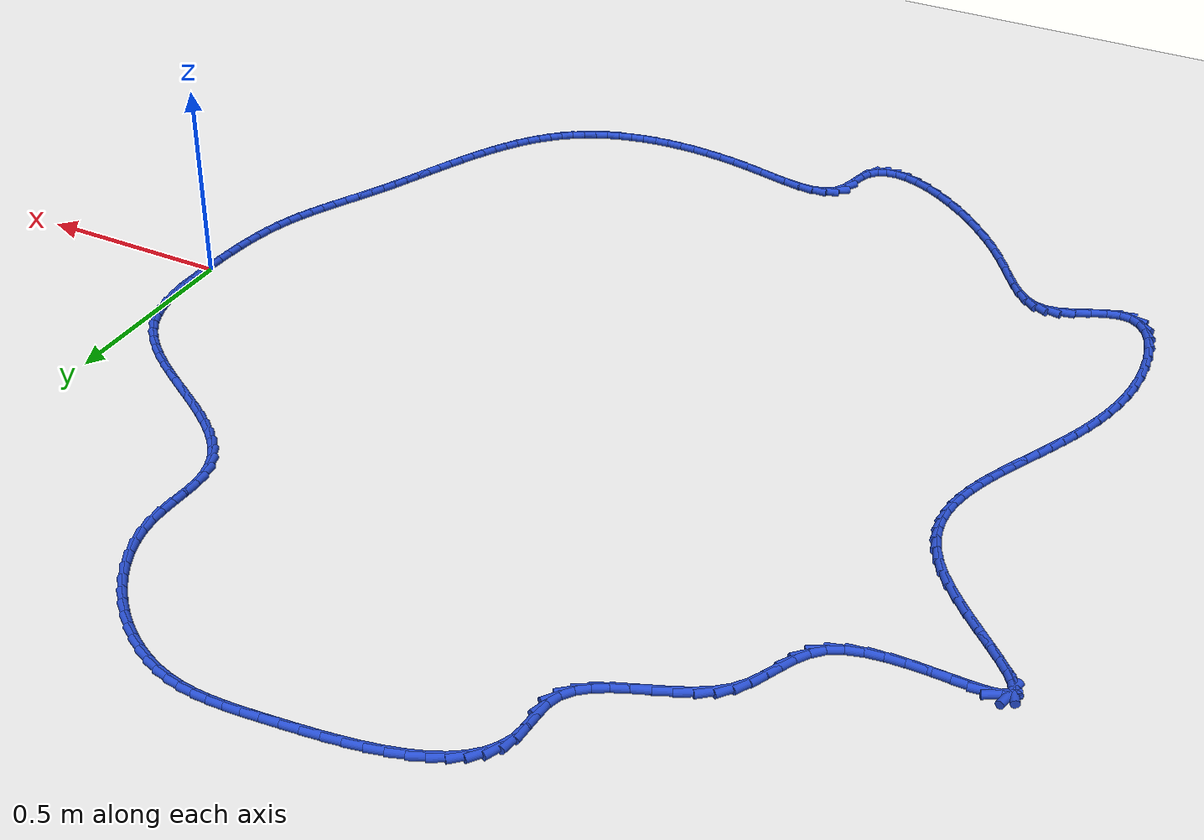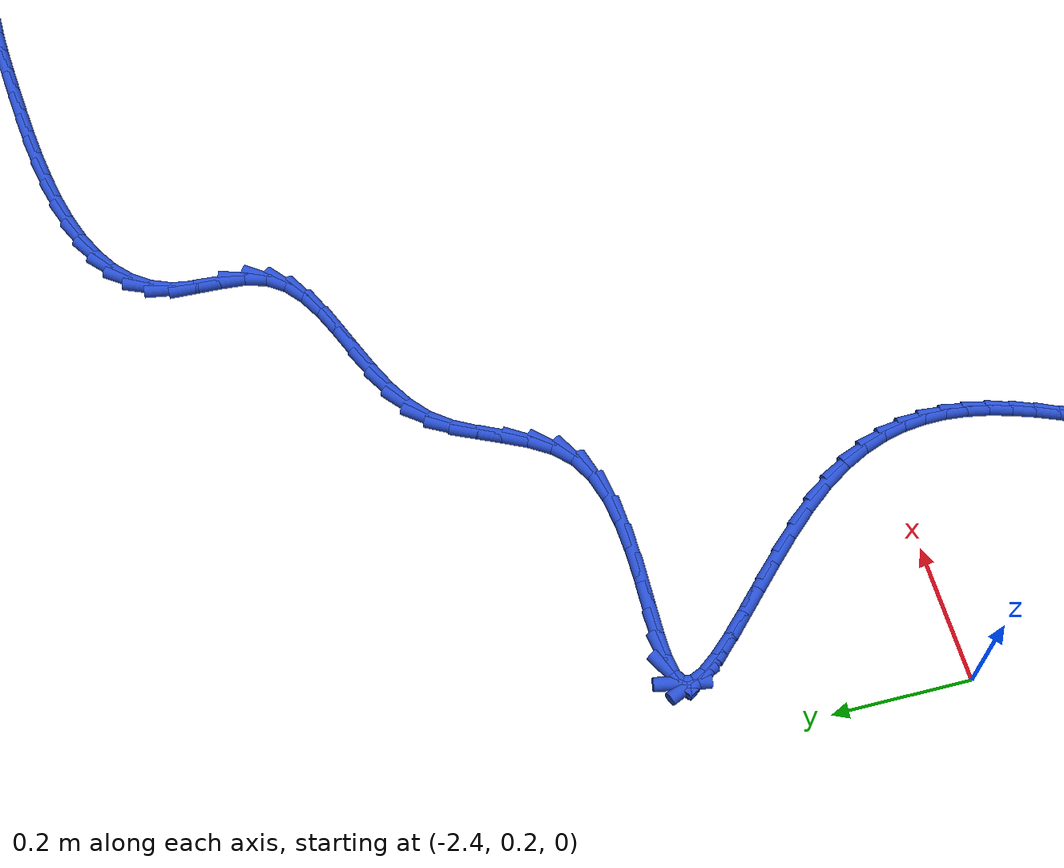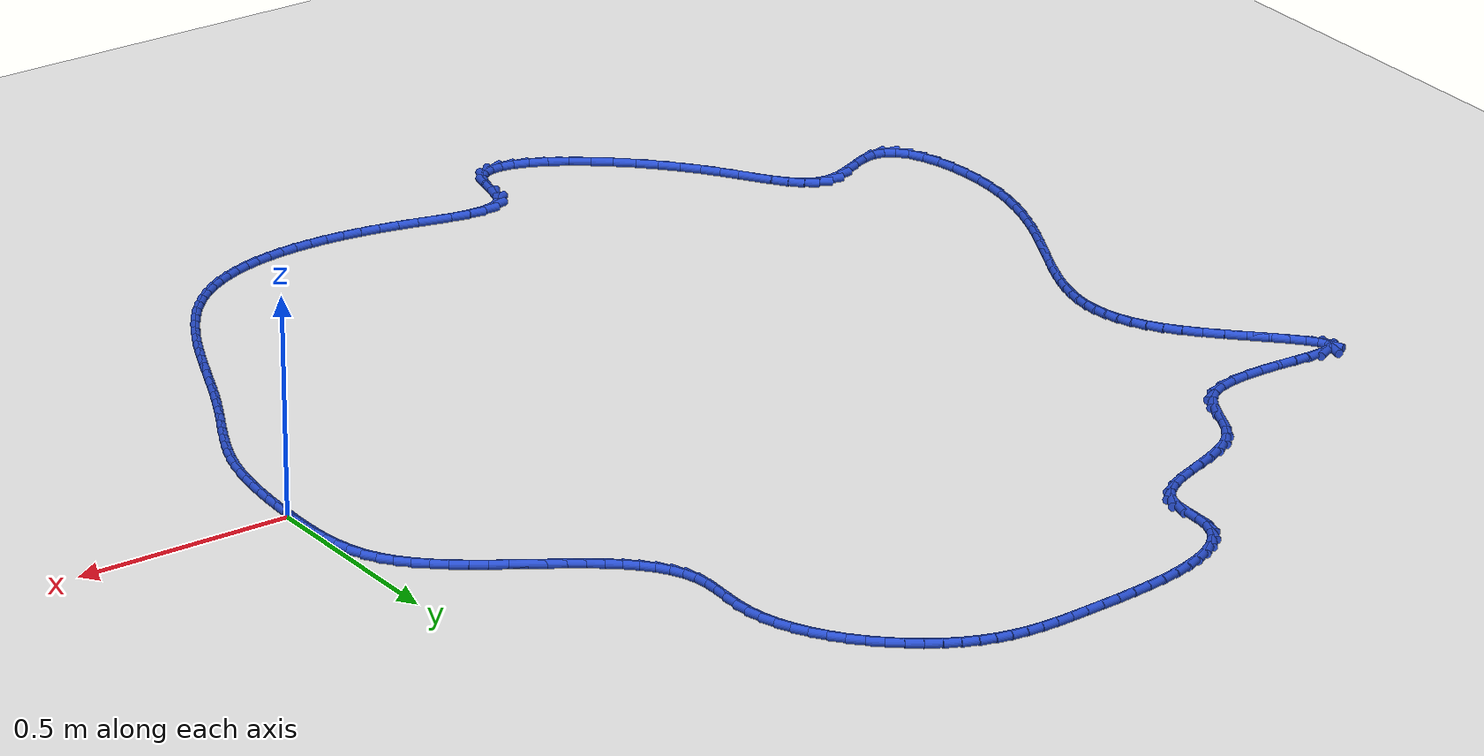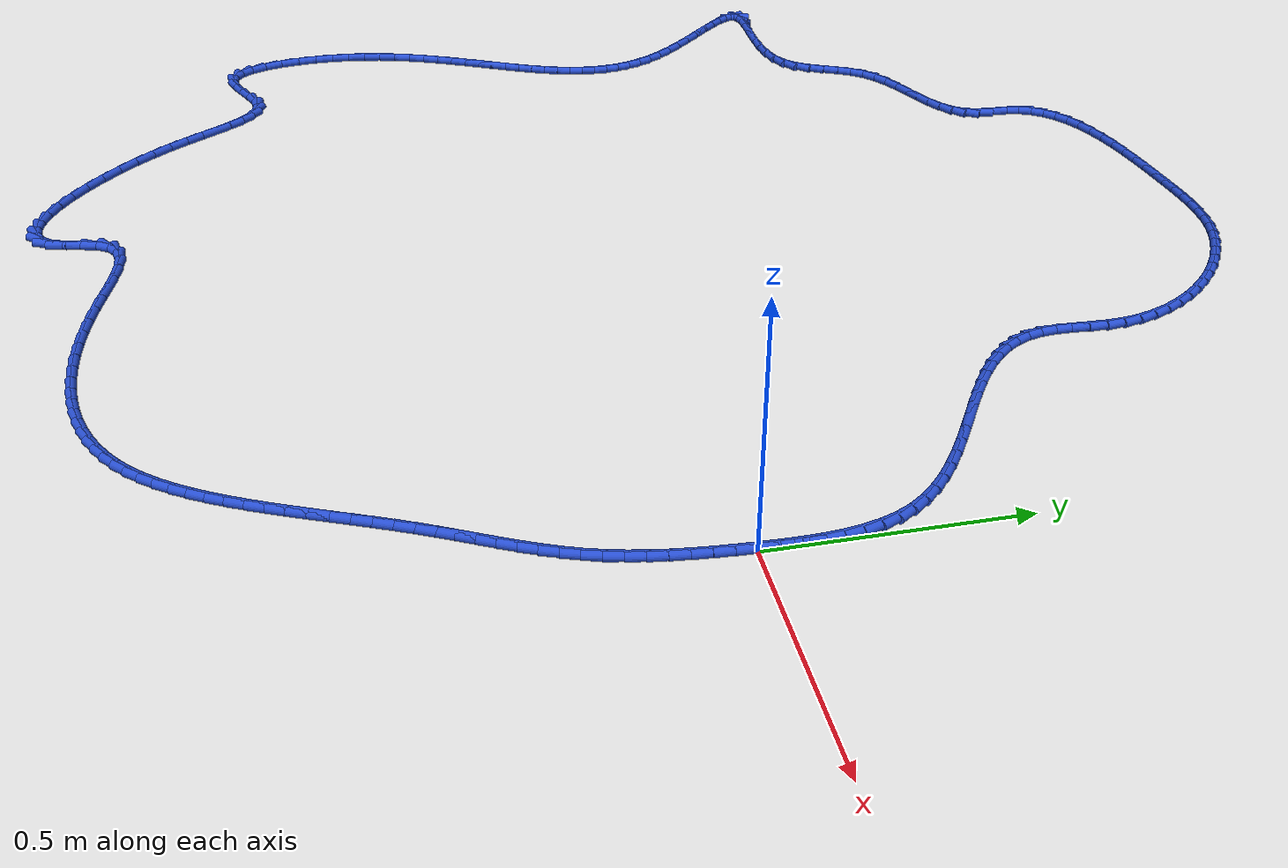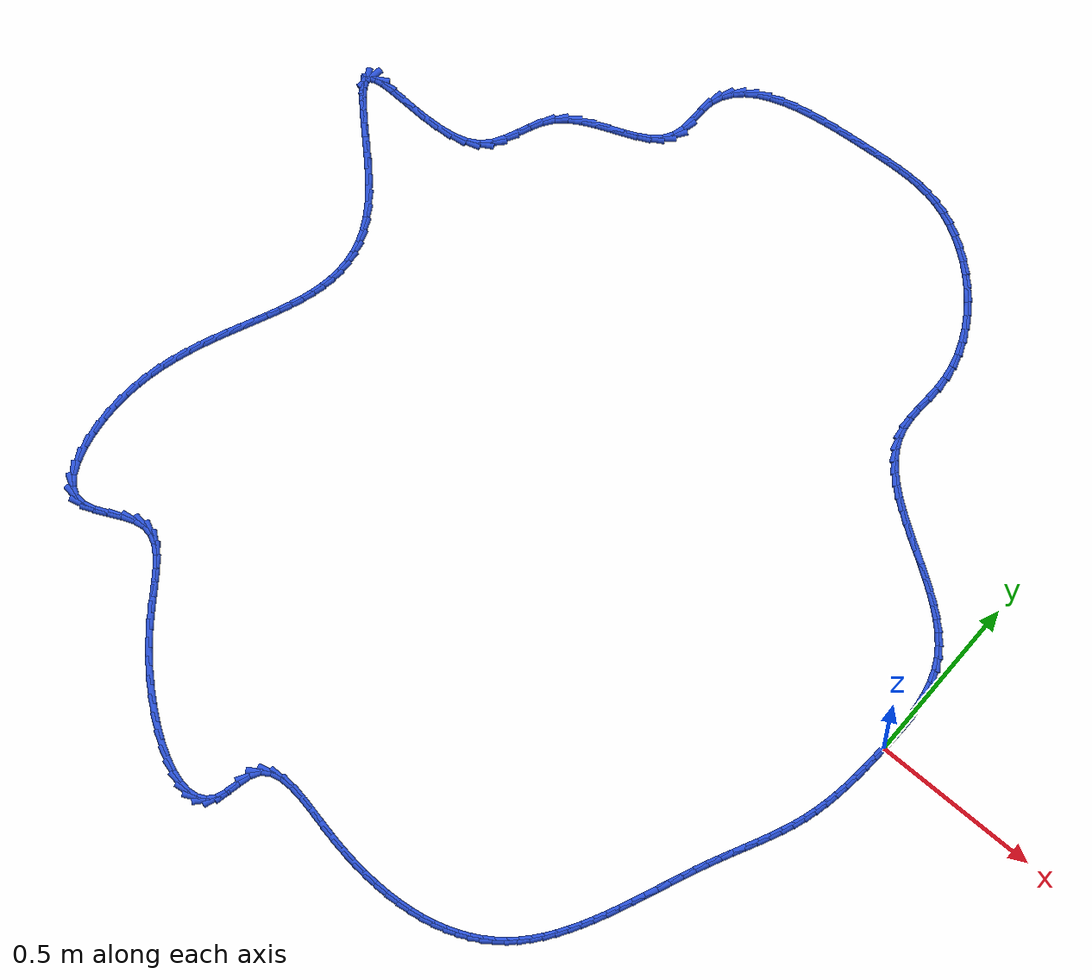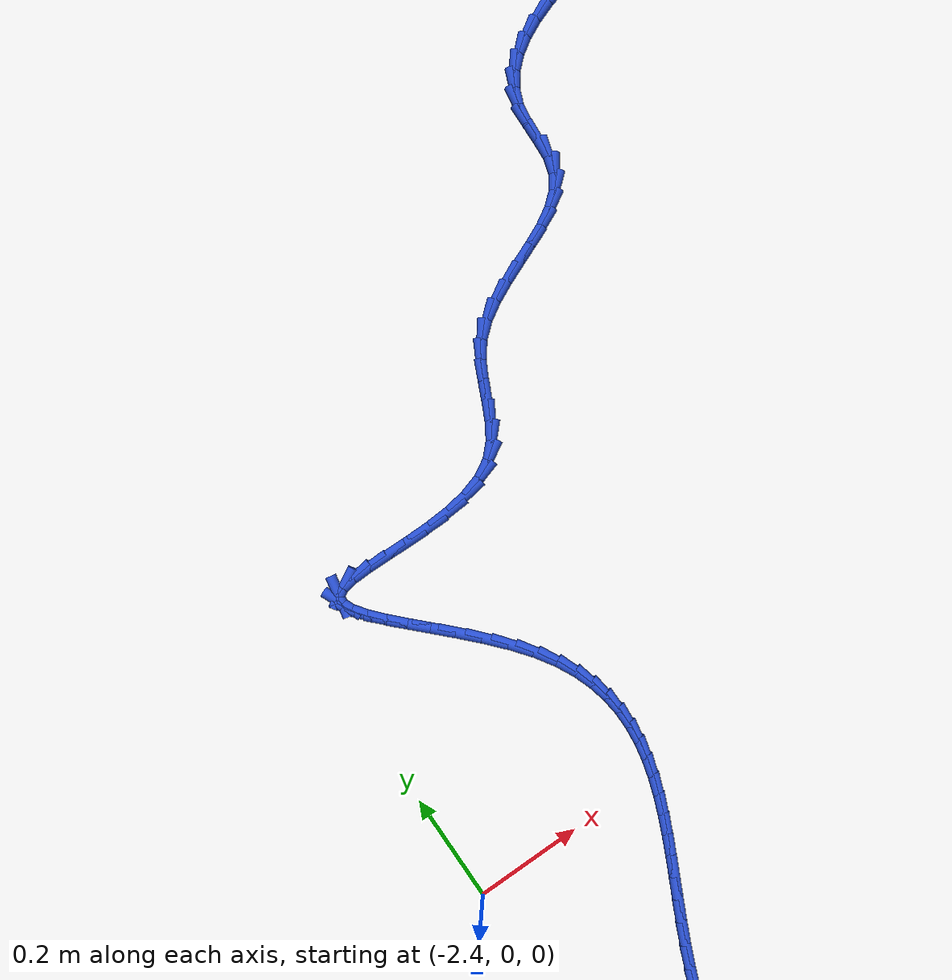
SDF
<sdf version="1.6">
 <world name="default">
  <light name="sun" type="directional">
   <pose>0 0 10 0 -0 0</pose>
   <diffuse>0.8 0.8 0.8 1</diffuse>
   <specular>0.2 0.2 0.2 1</specular>
   <attenuation>
    <range>1000</range>
    <constant>0.9</constant>
    <linear>0.01</linear>
    <quadratic>0.001</quadratic>
   </attenuation>
   <direction>-0.5 0.1 -0.9</direction>
  </light>
  <model name="ground_plane">
   <static>1</static>
   <link name="link">
    <collision name="collision">
     <geometry><plane><normal>0 0 1</normal><size>100 100</size></plane></geometry>
     <surface><friction><ode><mu>100</mu><mu2>50</mu2></ode></friction></surface>
    </collision>
    <visual name="visual">
     <cast_shadows>0</cast_shadows>
     <geometry><plane><normal>0 0 1</normal><size>100 100</size></plane></geometry>
     <material>
      <script><uri>file://media/materials/scripts/gazebo.material</uri><name>Gazebo/WhiteGlow</name></script>
     </material>
    </visual>
   </link>
  </model>
  <gravity>0 0 -9.8</gravity>
  <magnetic_field>6e-06 2.3e-05 -4.2e-05</magnetic_field>
  <atmosphere type="adiabatic"/>
  <physics name="default_physics" default="0" type="ode">
   <max_step_size>0.001</max_step_size>
   <real_time_factor>1</real_time_factor>
   <real_time_update_rate>1000</real_time_update_rate>
  </physics>
  <scene><ambient>0.4 0.4 0.4 1</ambient><background>0.7 0.7 0.7 1</background><shadows>1</shadows></scene>
  <spherical_coordinates>
   <surface_model>EARTH_WGS84</surface_model>
   <latitude_deg>0</latitude_deg>
   <longitude_deg>0</longitude_deg>
   <elevation>0</elevation>
   <heading_deg>0</heading_deg>
  </spherical_coordinates>
  <model name="line">
   <link name="link_0">
    <pose>-1.2197274440461925e-17 6.938893903907228e-18 0.01 0 1.57 1.5378652653499347</pose>
    <collision name="collision">
     <geometry><cylinder><radius>0.01</radius><length>0.08</length></cylinder></geometry>
    </collision>
    <visual name="visual">
     <material>
      <script><name>Gazebo/Blue</name><uri>file://media/materials/scripts/gazebo.material</uri></script>
     </material>
     <geometry><cylinder><radius>0.01</radius><length>0.08</length></cylinder></geometry>
    </visual>
   </link>
   <link name="link_1">
    <pose>0.0012553249739792628 0.03810600402900259 0.01 0 1.57 1.5622024554582632</pose>
    <collision name="collision">
     <geometry><cylinder><radius>0.01</radius><length>0.08</length></cylinder></geometry>
    </collision>
    <visual name="visual">
     <material>
      <script><name>Gazebo/Blue</name><uri>file://media/materials/scripts/gazebo.material</uri></script>
     </material>
     <geometry><cylinder><radius>0.01</radius><length>0.08</length></cylinder></geometry>
    </visual>
   </link>
   <link name="link_2">
    <pose>0.0015832489925126816 0.07626295713511785 0.01 0 1.57 -1.5416689976008755</pose>
    <collision name="collision">
     <geometry><cylinder><radius>0.01</radius><length>0.08</length></cylinder></geometry>
    </collision>
    <visual name="visual">
     <material>
      <script><name>Gazebo/Blue</name><uri>file://media/materials/scripts/gazebo.material</uri></script>
     </material>
     <geometry><cylinder><radius>0.01</radius><length>0.08</length></cylinder></geometry>
    </visual>
   </link>
   <link name="link_3">
    <pose>0.00047945373452400663 0.11414775869731687 0.01 0 1.57 -1.489456489503865</pose>
    <collision name="collision">
     <geometry><cylinder><radius>0.01</radius><length>0.08</length></cylinder></geometry>
    </collision>
    <visual name="visual">
     <material>
      <script><name>Gazebo/Blue</name><uri>file://media/materials/scripts/gazebo.material</uri></script>
     </material>
     <geometry><cylinder><radius>0.01</radius><length>0.08</length></cylinder></geometry>
    </visual>
   </link>
   <link name="link_4">
    <pose>-0.0025603791210629927 0.15143730809457104 0.01 0 1.57 -1.4212474075831878</pose>
    <collision name="collision">
     <geometry><cylinder><radius>0.01</radius><length>0.08</length></cylinder></geometry>
    </collision>
    <visual name="visual">
     <material>
      <script><name>Gazebo/Blue</name><uri>file://media/materials/scripts/gazebo.material</uri></script>
     </material>
     <geometry><cylinder><radius>0.01</radius><length>0.08</length></cylinder></geometry>
    </visual>
   </link>
   <link name="link_5">
    <pose>-0.008040567895324554 0.18780850470585142 0.01 0 1.57 -1.3354202576772765</pose>
    <collision name="collision">
     <geometry><cylinder><radius>0.01</radius><length>0.08</length></cylinder></geometry>
    </collision>
    <visual name="visual">
     <material>
      <script><name>Gazebo/Blue</name><uri>file://media/materials/scripts/gazebo.material</uri></script>
     </material>
     <geometry><cylinder><radius>0.01</radius><length>0.08</length></cylinder></geometry>
    </visual>
   </link>
   <link name="link_6">
    <pose>-0.016465430909336908 0.22293824791012934 0.01 0 1.57 -1.2307801653168424</pose>
    <collision name="collision">
     <geometry><cylinder><radius>0.01</radius><length>0.08</length></cylinder></geometry>
    </collision>
    <visual name="visual">
     <material>
      <script><name>Gazebo/Blue</name><uri>file://media/materials/scripts/gazebo.material</uri></script>
     </material>
     <geometry><cylinder><radius>0.01</radius><length>0.08</length></cylinder></geometry>
    </visual>
   </link>
   <link name="link_7">
    <pose>-0.02833928648417628 0.25650343708637585 0.01 0 1.57 -1.1074930269205026</pose>
    <collision name="collision">
     <geometry><cylinder><radius>0.01</radius><length>0.08</length></cylinder></geometry>
    </collision>
    <visual name="visual">
     <material>
      <script><name>Gazebo/Blue</name><uri>file://media/materials/scripts/gazebo.material</uri></script>
     </material>
     <geometry><cylinder><radius>0.01</radius><length>0.08</length></cylinder></geometry>
    </visual>
   </link>
   <link name="link_8">
    <pose>-0.04416485528396204 0.28818183789981355 0.01 0 1.57 -0.9776399475191118</pose>
    <collision name="collision">
     <geometry><cylinder><radius>0.01</radius><length>0.08</length></cylinder></geometry>
    </collision>
    <visual name="visual">
     <material>
      <script><name>Gazebo/Blue</name><uri>file://media/materials/scripts/gazebo.material</uri></script>
     </material>
     <geometry><cylinder><radius>0.01</radius><length>0.08</length></cylinder></geometry>
    </visual>
   </link>
   <link name="link_9">
    <pose>-0.06414196355037402 0.31781545231973096 0.01 0 1.57 -0.865268293751687</pose>
    <collision name="collision">
     <geometry><cylinder><radius>0.01</radius><length>0.08</length></cylinder></geometry>
    </collision>
    <visual name="visual">
     <material>
      <script><name>Gazebo/Blue</name><uri>file://media/materials/scripts/gazebo.material</uri></script>
     </material>
     <geometry><cylinder><radius>0.01</radius><length>0.08</length></cylinder></geometry>
    </visual>
   </link>
   <link name="link_10">
    <pose>-0.08781143223741854 0.3456036100995852 0.01 0 1.57 -0.7735691061702502</pose>
    <collision name="collision">
     <geometry><cylinder><radius>0.01</radius><length>0.08</length></cylinder></geometry>
    </collision>
    <visual name="visual">
     <material>
      <script><name>Gazebo/Blue</name><uri>file://media/materials/scripts/gazebo.material</uri></script>
     </material>
     <geometry><cylinder><radius>0.01</radius><length>0.08</length></cylinder></geometry>
    </visual>
   </link>
   <link name="link_11">
    <pose>-0.11462746030926872 0.37179260942277814 0.01 0 1.57 -0.7011665936191535</pose>
    <collision name="collision">
     <geometry><cylinder><radius>0.01</radius><length>0.08</length></cylinder></geometry>
    </collision>
    <visual name="visual">
     <material>
      <script><name>Gazebo/Blue</name><uri>file://media/materials/scripts/gazebo.material</uri></script>
     </material>
     <geometry><cylinder><radius>0.01</radius><length>0.08</length></cylinder></geometry>
    </visual>
   </link>
   <link name="link_12">
    <pose>-0.14404424673009783 0.396628748472712 0.01 0 1.57 -0.6460538107792938</pose>
    <collision name="collision">
     <geometry><cylinder><radius>0.01</radius><length>0.08</length></cylinder></geometry>
    </collision>
    <visual name="visual">
     <material>
      <script><name>Gazebo/Blue</name><uri>file://media/materials/scripts/gazebo.material</uri></script>
     </material>
     <geometry><cylinder><radius>0.01</radius><length>0.08</length></cylinder></geometry>
    </visual>
   </link>
   <link name="link_13">
    <pose>-0.17551599046407892 0.4203583254327884 0.01 0 1.57 -0.6062899957121826</pose>
    <collision name="collision">
     <geometry><cylinder><radius>0.01</radius><length>0.08</length></cylinder></geometry>
    </collision>
    <visual name="visual">
     <material>
      <script><name>Gazebo/Blue</name><uri>file://media/materials/scripts/gazebo.material</uri></script>
     </material>
     <geometry><cylinder><radius>0.01</radius><length>0.08</length></cylinder></geometry>
    </visual>
   </link>
   <link name="link_14">
    <pose>-0.2084968904753851 0.4432276384864097 0.01 0 1.57 -0.5803326571098348</pose>
    <collision name="collision">
     <geometry><cylinder><radius>0.01</radius><length>0.08</length></cylinder></geometry>
    </collision>
    <visual name="visual">
     <material>
      <script><name>Gazebo/Blue</name><uri>file://media/materials/scripts/gazebo.material</uri></script>
     </material>
     <geometry><cylinder><radius>0.01</radius><length>0.08</length></cylinder></geometry>
    </visual>
   </link>
   <link name="link_15">
    <pose>-0.24244114572818976 0.4654829858169777 0.01 0 1.57 -0.5671656148158033</pose>
    <collision name="collision">
     <geometry><cylinder><radius>0.01</radius><length>0.08</length></cylinder></geometry>
    </collision>
    <visual name="visual">
     <material>
      <script><name>Gazebo/Blue</name><uri>file://media/materials/scripts/gazebo.material</uri></script>
     </material>
     <geometry><cylinder><radius>0.01</radius><length>0.08</length></cylinder></geometry>
    </visual>
   </link>
   <link name="link_16">
    <pose>-0.27680295518666576 0.4873706656078943 0.01 0 1.57 -0.5663406551424146</pose>
    <collision name="collision">
     <geometry><cylinder><radius>0.01</radius><length>0.08</length></cylinder></geometry>
    </collision>
    <visual name="visual">
     <material>
      <script><name>Gazebo/Blue</name><uri>file://media/materials/scripts/gazebo.material</uri></script>
     </material>
     <geometry><cylinder><radius>0.01</radius><length>0.08</length></cylinder></geometry>
    </visual>
   </link>
   <link name="link_17">
    <pose>-0.31103651781498654 0.5091369760425618 0.01 0 1.57 -0.577998081288668</pose>
    <collision name="collision">
     <geometry><cylinder><radius>0.01</radius><length>0.08</length></cylinder></geometry>
    </collision>
    <visual name="visual">
     <material>
      <script><name>Gazebo/Blue</name><uri>file://media/materials/scripts/gazebo.material</uri></script>
     </material>
     <geometry><cylinder><radius>0.01</radius><length>0.08</length></cylinder></geometry>
    </visual>
   </link>
   <link name="link_18">
    <pose>-0.3445960325773251 0.5310282153043822 0.01 0 1.57 -0.602894879391475</pose>
    <collision name="collision">
     <geometry><cylinder><radius>0.01</radius><length>0.08</length></cylinder></geometry>
    </collision>
    <visual name="visual">
     <material>
      <script><name>Gazebo/Blue</name><uri>file://media/materials/scripts/gazebo.material</uri></script>
     </material>
     <geometry><cylinder><radius>0.01</radius><length>0.08</length></cylinder></geometry>
    </visual>
   </link>
   <link name="link_19">
    <pose>-0.37693569843785457 0.553290681576757 0.01 0 1.57 -0.6424427343244258</pose>
    <collision name="collision">
     <geometry><cylinder><radius>0.01</radius><length>0.08</length></cylinder></geometry>
    </collision>
    <visual name="visual">
     <material>
      <script><name>Gazebo/Blue</name><uri>file://media/materials/scripts/gazebo.material</uri></script>
     </material>
     <geometry><cylinder><radius>0.01</radius><length>0.08</length></cylinder></geometry>
    </visual>
   </link>
   <link name="link_20">
    <pose>-0.4075097143607482 0.5761706730430886 0.01 0 1.57 -0.6987274551730457</pose>
    <collision name="collision">
     <geometry><cylinder><radius>0.01</radius><length>0.08</length></cylinder></geometry>
    </collision>
    <visual name="visual">
     <material>
      <script><name>Gazebo/Blue</name><uri>file://media/materials/scripts/gazebo.material</uri></script>
     </material>
     <geometry><cylinder><radius>0.01</radius><length>0.08</length></cylinder></geometry>
    </visual>
   </link>
   <link name="link_21">
    <pose>-0.4357722793101789 0.5999144878867787 0.01 0 1.57 -0.7744279554427321</pose>
    <collision name="collision">
     <geometry><cylinder><radius>0.01</radius><length>0.08</length></cylinder></geometry>
    </collision>
    <visual name="visual">
     <material>
      <script><name>Gazebo/Blue</name><uri>file://media/materials/scripts/gazebo.material</uri></script>
     </material>
     <geometry><cylinder><radius>0.01</radius><length>0.08</length></cylinder></geometry>
    </visual>
   </link>
   <link name="link_22">
    <pose>-0.46117759225032023 0.6247684242912297 0.01 0 1.57 -0.872459584215574</pose>
    <collision name="collision">
     <geometry><cylinder><radius>0.01</radius><length>0.08</length></cylinder></geometry>
    </collision>
    <visual name="visual">
     <material>
      <script><name>Gazebo/Blue</name><uri>file://media/materials/scripts/gazebo.material</uri></script>
     </material>
     <geometry><cylinder><radius>0.01</radius><length>0.08</length></cylinder></geometry>
    </visual>
   </link>
   <link name="link_23">
    <pose>-0.48317985214534515 0.6509787804398434 0.01 0 1.57 -0.9950555875091925</pose>
    <collision name="collision">
     <geometry><cylinder><radius>0.01</radius><length>0.08</length></cylinder></geometry>
    </collision>
    <visual name="visual">
     <material>
      <script><name>Gazebo/Blue</name><uri>file://media/materials/scripts/gazebo.material</uri></script>
     </material>
     <geometry><cylinder><radius>0.01</radius><length>0.08</length></cylinder></geometry>
    </visual>
   </link>
   <link name="link_24">
    <pose>-0.5012332579594266 0.6787918545160216 0.01 0 1.57 -1.1420479130836112</pose>
    <collision name="collision">
     <geometry><cylinder><radius>0.01</radius><length>0.08</length></cylinder></geometry>
    </collision>
    <visual name="visual">
     <material>
      <script><name>Gazebo/Blue</name><uri>file://media/materials/scripts/gazebo.material</uri></script>
     </material>
     <geometry><cylinder><radius>0.01</radius><length>0.08</length></cylinder></geometry>
    </visual>
   </link>
   <link name="link_25">
    <pose>-0.5147920086567381 0.7084539447031666 0.01 0 1.57 -1.3087347858568719</pose>
    <collision name="collision">
     <geometry><cylinder><radius>0.01</radius><length>0.08</length></cylinder></geometry>
    </collision>
    <visual name="visual">
     <material>
      <script><name>Gazebo/Blue</name><uri>file://media/materials/scripts/gazebo.material</uri></script>
     </material>
     <geometry><cylinder><radius>0.01</radius><length>0.08</length></cylinder></geometry>
    </visual>
   </link>
   <link name="link_26">
    <pose>-0.5233103032014527 0.7402113491846801 0.01 0 1.57 -1.4740119377629726</pose>
    <collision name="collision">
     <geometry><cylinder><radius>0.01</radius><length>0.08</length></cylinder></geometry>
    </collision>
    <visual name="visual">
     <material>
      <script><name>Gazebo/Blue</name><uri>file://media/materials/scripts/gazebo.material</uri></script>
     </material>
     <geometry><cylinder><radius>0.01</radius><length>0.08</length></cylinder></geometry>
    </visual>
   </link>
   <link name="link_27">
    <pose>-0.5266100318350425 0.7741984325792118 0.01 0 1.57 1.5613481809451468</pose>
    <collision name="collision">
     <geometry><cylinder><radius>0.01</radius><length>0.08</length></cylinder></geometry>
    </collision>
    <visual name="visual">
     <material>
      <script><name>Gazebo/Blue</name><uri>file://media/materials/scripts/gazebo.material</uri></script>
     </material>
     <geometry><cylinder><radius>0.01</radius><length>0.08</length></cylinder></geometry>
    </visual>
   </link>
   <link name="link_28">
    <pose>-0.5262716289939188 0.8100142187653184 0.01 0 1.57 1.5203862530306893</pose>
    <collision name="collision">
     <geometry><cylinder><radius>0.01</radius><length>0.08</length></cylinder></geometry>
    </collision>
    <visual name="visual">
     <material>
      <script><name>Gazebo/Blue</name><uri>file://media/materials/scripts/gazebo.material</uri></script>
     </material>
     <geometry><cylinder><radius>0.01</radius><length>0.08</length></cylinder></geometry>
    </visual>
   </link>
   <link name="link_29">
    <pose>-0.5244006542240386 0.8470978716273672 0.01 0 1.57 1.5364655016082054</pose>
    <collision name="collision">
     <geometry><cylinder><radius>0.01</radius><length>0.08</length></cylinder></geometry>
    </collision>
    <visual name="visual">
     <material>
      <script><name>Gazebo/Blue</name><uri>file://media/materials/scripts/gazebo.material</uri></script>
     </material>
     <geometry><cylinder><radius>0.01</radius><length>0.08</length></cylinder></geometry>
    </visual>
   </link>
   <link name="link_30">
    <pose>-0.5231027599061153 0.8848885267887207 0.01 0 1.57 -1.5344339505536866</pose>
    <collision name="collision">
     <geometry><cylinder><radius>0.01</radius><length>0.08</length></cylinder></geometry>
    </collision>
    <visual name="visual">
     <material>
      <script><name>Gazebo/Blue</name><uri>file://media/materials/scripts/gazebo.material</uri></script>
     </material>
     <geometry><cylinder><radius>0.01</radius><length>0.08</length></cylinder></geometry>
    </visual>
   </link>
   <link name="link_31">
    <pose>-0.5244828437341927 0.9228254180977429 0.01 0 1.57 -1.4231509830541502</pose>
    <collision name="collision">
     <geometry><cylinder><radius>0.01</radius><length>0.08</length></cylinder></geometry>
    </collision>
    <visual name="visual">
     <material>
      <script><name>Gazebo/Blue</name><uri>file://media/materials/scripts/gazebo.material</uri></script>
     </material>
     <geometry><cylinder><radius>0.01</radius><length>0.08</length></cylinder></geometry>
    </visual>
   </link>
   <link name="link_32">
    <pose>-0.5300745142541082 0.9604221346020347 0.01 0 1.57 -1.3130007746534529</pose>
    <collision name="collision">
     <geometry><cylinder><radius>0.01</radius><length>0.08</length></cylinder></geometry>
    </collision>
    <visual name="visual">
     <material>
      <script><name>Gazebo/Blue</name><uri>file://media/materials/scripts/gazebo.material</uri></script>
     </material>
     <geometry><cylinder><radius>0.01</radius><length>0.08</length></cylinder></geometry>
    </visual>
   </link>
   <link name="link_33">
    <pose>-0.5398238947844056 0.9973988818773287 0.01 0 1.57 -1.2111162126619603</pose>
    <collision name="collision">
     <geometry><cylinder><radius>0.01</radius><length>0.08</length></cylinder></geometry>
    </collision>
    <visual name="visual">
     <material>
      <script><name>Gazebo/Blue</name><uri>file://media/materials/scripts/gazebo.material</uri></script>
     </material>
     <geometry><cylinder><radius>0.01</radius><length>0.08</length></cylinder></geometry>
    </visual>
   </link>
   <link name="link_34">
    <pose>-0.5534035871602542 1.0335114652380466 0.01 0 1.57 -1.116782160486267</pose>
    <collision name="collision">
     <geometry><cylinder><radius>0.01</radius><length>0.08</length></cylinder></geometry>
    </collision>
    <visual name="visual">
     <material>
      <script><name>Gazebo/Blue</name><uri>file://media/materials/scripts/gazebo.material</uri></script>
     </material>
     <geometry><cylinder><radius>0.01</radius><length>0.08</length></cylinder></geometry>
    </visual>
   </link>
   <link name="link_35">
    <pose>-0.570486193216822 1.0685156899986097 0.01 0 1.57 -1.0289115634188921</pose>
    <collision name="collision">
     <geometry><cylinder><radius>0.01</radius><length>0.08</length></cylinder></geometry>
    </collision>
    <visual name="visual">
     <material>
      <script><name>Gazebo/Blue</name><uri>file://media/materials/scripts/gazebo.material</uri></script>
     </material>
     <geometry><cylinder><radius>0.01</radius><length>0.08</length></cylinder></geometry>
    </visual>
   </link>
   <link name="link_36">
    <pose>-0.5907443147892778 1.1021673614734402 0.01 0 1.57 -0.9462250457985829</pose>
    <collision name="collision">
     <geometry><cylinder><radius>0.01</radius><length>0.08</length></cylinder></geometry>
    </collision>
    <visual name="visual">
     <material>
      <script><name>Gazebo/Blue</name><uri>file://media/materials/scripts/gazebo.material</uri></script>
     </material>
     <geometry><cylinder><radius>0.01</radius><length>0.08</length></cylinder></geometry>
    </visual>
   </link>
   <link name="link_37">
    <pose>-0.6138505537127904 1.1342222849769592 0.01 0 1.57 -0.8673585869584852</pose>
    <collision name="collision">
     <geometry><cylinder><radius>0.01</radius><length>0.08</length></cylinder></geometry>
    </collision>
    <visual name="visual">
     <material>
      <script><name>Gazebo/Blue</name><uri>file://media/materials/scripts/gazebo.material</uri></script>
     </material>
     <geometry><cylinder><radius>0.01</radius><length>0.08</length></cylinder></geometry>
    </visual>
   </link>
   <link name="link_38">
    <pose>-0.639477511822528 1.1644362658235883 0.01 0 1.57 -0.7909131961647354</pose>
    <collision name="collision">
     <geometry><cylinder><radius>0.01</radius><length>0.08</length></cylinder></geometry>
    </collision>
    <visual name="visual">
     <material>
      <script><name>Gazebo/Blue</name><uri>file://media/materials/scripts/gazebo.material</uri></script>
     </material>
     <geometry><cylinder><radius>0.01</radius><length>0.08</length></cylinder></geometry>
    </visual>
   </link>
   <link name="link_39">
    <pose>-0.6672977909536592 1.1925651093277492 0.01 0 1.57 -0.7154639071690265</pose>
    <collision name="collision">
     <geometry><cylinder><radius>0.01</radius><length>0.08</length></cylinder></geometry>
    </collision>
    <visual name="visual">
     <material>
      <script><name>Gazebo/Blue</name><uri>file://media/materials/scripts/gazebo.material</uri></script>
     </material>
     <geometry><cylinder><radius>0.01</radius><length>0.08</length></cylinder></geometry>
    </visual>
   </link>
   <link name="link_40">
    <pose>-0.6969839929413528 1.2183646208038634 0.01 0 1.57 -0.639542585867524</pose>
    <collision name="collision">
     <geometry><cylinder><radius>0.01</radius><length>0.08</length></cylinder></geometry>
    </collision>
    <visual name="visual">
     <material>
      <script><name>Gazebo/Blue</name><uri>file://media/materials/scripts/gazebo.material</uri></script>
     </material>
     <geometry><cylinder><radius>0.01</radius><length>0.08</length></cylinder></geometry>
    </visual>
   </link>
   <link name="link_41">
    <pose>-0.7282087196207772 1.2415906055663526 0.01 0 1.57 -0.5616055477025852</pose>
    <collision name="collision">
     <geometry><cylinder><radius>0.01</radius><length>0.08</length></cylinder></geometry>
    </collision>
    <visual name="visual">
     <material>
      <script><name>Gazebo/Blue</name><uri>file://media/materials/scripts/gazebo.material</uri></script>
     </material>
     <geometry><cylinder><radius>0.01</radius><length>0.08</length></cylinder></geometry>
    </visual>
   </link>
   <link name="link_42">
    <pose>-0.760644572827101 1.2619988689296384 0.01 0 1.57 -0.4799955558753285</pose>
    <collision name="collision">
     <geometry><cylinder><radius>0.01</radius><length>0.08</length></cylinder></geometry>
    </collision>
    <visual name="visual">
     <material>
      <script><name>Gazebo/Blue</name><uri>file://media/materials/scripts/gazebo.material</uri></script>
     </material>
     <geometry><cylinder><radius>0.01</radius><length>0.08</length></cylinder></geometry>
    </visual>
   </link>
   <link name="link_43">
    <pose>-0.7939641543954931 1.279345216208143 0.01 0 1.57 -0.39291006900240555</pose>
    <collision name="collision">
     <geometry><cylinder><radius>0.01</radius><length>0.08</length></cylinder></geometry>
    </collision>
    <visual name="visual">
     <material>
      <script><name>Gazebo/Blue</name><uri>file://media/materials/scripts/gazebo.material</uri></script>
     </material>
     <geometry><cylinder><radius>0.01</radius><length>0.08</length></cylinder></geometry>
    </visual>
   </link>
   <link name="link_44">
    <pose>-0.8278400661611217 1.293385452716287 0.01 0 1.57 -0.2986195110437447</pose>
    <collision name="collision">
     <geometry><cylinder><radius>0.01</radius><length>0.08</length></cylinder></geometry>
    </collision>
    <visual name="visual">
     <material>
      <script><name>Gazebo/Blue</name><uri>file://media/materials/scripts/gazebo.material</uri></script>
     </material>
     <geometry><cylinder><radius>0.01</radius><length>0.08</length></cylinder></geometry>
    </visual>
   </link>
   <link name="link_45">
    <pose>-0.8619540198410135 1.3038865568959812 0.01 0 1.57 -0.20281036869704078</pose>
    <collision name="collision">
     <geometry><cylinder><radius>0.01</radius><length>0.08</length></cylinder></geometry>
    </collision>
    <visual name="visual">
     <material>
      <script><name>Gazebo/Blue</name><uri>file://media/materials/scripts/gazebo.material</uri></script>
     </material>
     <geometry><cylinder><radius>0.01</radius><length>0.08</length></cylinder></geometry>
    </visual>
   </link>
   <link name="link_46">
    <pose>-0.89625187873056 1.3109394849648546 0.01 0 1.57 -0.11644165517910625</pose>
    <collision name="collision">
     <geometry><cylinder><radius>0.01</radius><length>0.08</length></cylinder></geometry>
    </collision>
    <visual name="visual">
     <material>
      <script><name>Gazebo/Blue</name><uri>file://media/materials/scripts/gazebo.material</uri></script>
     </material>
     <geometry><cylinder><radius>0.01</radius><length>0.08</length></cylinder></geometry>
    </visual>
   </link>
   <link name="link_47">
    <pose>-0.9309781221933072 1.3150014410734607 0.01 0 1.57 -0.04367823381119316</pose>
    <collision name="collision">
     <geometry><cylinder><radius>0.01</radius><length>0.08</length></cylinder></geometry>
    </collision>
    <visual name="visual">
     <material>
      <script><name>Gazebo/Blue</name><uri>file://media/materials/scripts/gazebo.material</uri></script>
     </material>
     <geometry><cylinder><radius>0.01</radius><length>0.08</length></cylinder></geometry>
    </visual>
   </link>
   <link name="link_48">
    <pose>-0.9663932648859114 1.3165492964083276 0.01 0 1.57 0.013456639079492546</pose>
    <collision name="collision">
     <geometry><cylinder><radius>0.01</radius><length>0.08</length></cylinder></geometry>
    </collision>
    <visual name="visual">
     <material>
      <script><name>Gazebo/Blue</name><uri>file://media/materials/scripts/gazebo.material</uri></script>
     </material>
     <geometry><cylinder><radius>0.01</radius><length>0.08</length></cylinder></geometry>
    </visual>
   </link>
   <link name="link_49">
    <pose>-1.0027578214650283 1.316059922155985 0.01 0 1.57 0.05449716873527923</pose>
    <collision name="collision">
     <geometry><cylinder><radius>0.01</radius><length>0.08</length></cylinder></geometry>
    </collision>
    <visual name="visual">
     <material>
      <script><name>Gazebo/Blue</name><uri>file://media/materials/scripts/gazebo.material</uri></script>
     </material>
     <geometry><cylinder><radius>0.01</radius><length>0.08</length></cylinder></geometry>
    </visual>
   </link>
   <link name="link_50">
    <pose>-1.0403323065873136 1.3140101895029597 0.01 0 1.57 0.08007493946452095</pose>
    <collision name="collision">
     <geometry><cylinder><radius>0.01</radius><length>0.08</length></cylinder></geometry>
    </collision>
    <visual name="visual">
     <material>
      <script><name>Gazebo/Blue</name><uri>file://media/materials/scripts/gazebo.material</uri></script>
     </material>
     <geometry><cylinder><radius>0.01</radius><length>0.08</length></cylinder></geometry>
    </visual>
   </link>
   <link name="link_51">
    <pose>-1.0793772349094235 1.3108769696357812 0.01 0 1.57 0.0915739408658708</pose>
    <collision name="collision">
     <geometry><cylinder><radius>0.01</radius><length>0.08</length></cylinder></geometry>
    </collision>
    <visual name="visual">
     <material>
      <script><name>Gazebo/Blue</name><uri>file://media/materials/scripts/gazebo.material</uri></script>
     </material>
     <geometry><cylinder><radius>0.01</radius><length>0.08</length></cylinder></geometry>
    </visual>
   </link>
   <link name="link_52">
    <pose>-1.1201480342559114 1.3071329555107138 0.01 0 1.57 0.0981125445259163</pose>
    <collision name="collision">
     <geometry><cylinder><radius>0.01</radius><length>0.08</length></cylinder></geometry>
    </collision>
    <visual name="visual">
     <material>
      <script><name>Gazebo/Blue</name><uri>file://media/materials/scripts/gazebo.material</uri></script>
     </material>
     <geometry><cylinder><radius>0.01</radius><length>0.08</length></cylinder></geometry>
    </visual>
   </link>
   <link name="link_53">
    <pose>-1.162545806466998 1.302959803241977 0.01 0 1.57 0.1124877998662112</pose>
    <collision name="collision">
     <geometry><cylinder><radius>0.01</radius><length>0.08</length></cylinder></geometry>
    </collision>
    <visual name="visual">
     <material>
      <script><name>Gazebo/Blue</name><uri>file://media/materials/scripts/gazebo.material</uri></script>
     </material>
     <geometry><cylinder><radius>0.01</radius><length>0.08</length></cylinder></geometry>
    </visual>
   </link>
   <link name="link_54">
    <pose>-1.2058921739502846 1.2980631952033461 0.01 0 1.57 0.1359325334782057</pose>
    <collision name="collision">
     <geometry><cylinder><radius>0.01</radius><length>0.08</length></cylinder></geometry>
    </collision>
    <visual name="visual">
     <material>
      <script><name>Gazebo/Blue</name><uri>file://media/materials/scripts/gazebo.material</uri></script>
     </material>
     <geometry><cylinder><radius>0.01</radius><length>0.08</length></cylinder></geometry>
    </visual>
   </link>
   <link name="link_55">
    <pose>-1.2494551970570986 1.2921048188814008 0.01 0 1.57 0.16930082686875172</pose>
    <collision name="collision">
     <geometry><cylinder><radius>0.01</radius><length>0.08</length></cylinder></geometry>
    </collision>
    <visual name="visual">
     <material>
      <script><name>Gazebo/Blue</name><uri>file://media/materials/scripts/gazebo.material</uri></script>
     </material>
     <geometry><cylinder><radius>0.01</radius><length>0.08</length></cylinder></geometry>
    </visual>
   </link>
   <link name="link_56">
    <pose>-1.2925029361387688 1.2847463617627204 0.01 0 1.57 0.21428412550458614</pose>
    <collision name="collision">
     <geometry><cylinder><radius>0.01</radius><length>0.08</length></cylinder></geometry>
    </collision>
    <visual name="visual">
     <material>
      <script><name>Gazebo/Blue</name><uri>file://media/materials/scripts/gazebo.material</uri></script>
     </material>
     <geometry><cylinder><radius>0.01</radius><length>0.08</length></cylinder></geometry>
    </visual>
   </link>
   <link name="link_57">
    <pose>-1.3343034515466234 1.2756495113338853 0.01 0 1.57 0.27355765989172215</pose>
    <collision name="collision">
     <geometry><cylinder><radius>0.01</radius><length>0.08</length></cylinder></geometry>
    </collision>
    <visual name="visual">
     <material>
      <script><name>Gazebo/Blue</name><uri>file://media/materials/scripts/gazebo.material</uri></script>
     </material>
     <geometry><cylinder><radius>0.01</radius><length>0.08</length></cylinder></geometry>
    </visual>
   </link>
   <link name="link_58">
    <pose>-1.3741248036319897 1.2644759550814748 0.01 0 1.57 0.3510048901809385</pose>
    <collision name="collision">
     <geometry><cylinder><radius>0.01</radius><length>0.08</length></cylinder></geometry>
    </collision>
    <visual name="visual">
     <material>
      <script><name>Gazebo/Blue</name><uri>file://media/materials/scripts/gazebo.material</uri></script>
     </material>
     <geometry><cylinder><radius>0.01</radius><length>0.08</length></cylinder></geometry>
    </visual>
   </link>
   <link name="link_59">
    <pose>-1.411235052746197 1.2508873804920688 0.01 0 1.57 0.4518957733326471</pose>
    <collision name="collision">
     <geometry><cylinder><radius>0.01</radius><length>0.08</length></cylinder></geometry>
    </collision>
    <visual name="visual">
     <material>
      <script><name>Gazebo/Blue</name><uri>file://media/materials/scripts/gazebo.material</uri></script>
     </material>
     <geometry><cylinder><radius>0.01</radius><length>0.08</length></cylinder></geometry>
    </visual>
   </link>
   <link name="link_60">
    <pose>-1.4449022592405725 1.2345454750522478 0.01 0 1.57 0.5826329221952813</pose>
    <collision name="collision">
     <geometry><cylinder><radius>0.01</radius><length>0.08</length></cylinder></geometry>
    </collision>
    <visual name="visual">
     <material>
      <script><name>Gazebo/Blue</name><uri>file://media/materials/scripts/gazebo.material</uri></script>
     </material>
     <geometry><cylinder><radius>0.01</radius><length>0.08</length></cylinder></geometry>
    </visual>
   </link>
   <link name="link_61">
    <pose>-1.4743944834664449 1.21511192624859 0.01 0 1.57 0.749126598527334</pose>
    <collision name="collision">
     <geometry><cylinder><radius>0.01</radius><length>0.08</length></cylinder></geometry>
    </collision>
    <visual name="visual">
     <material>
      <script><name>Gazebo/Blue</name><uri>file://media/materials/scripts/gazebo.material</uri></script>
     </material>
     <geometry><cylinder><radius>0.01</radius><length>0.08</length></cylinder></geometry>
    </visual>
   </link>
   <link name="link_62">
    <pose>-1.4989797857751417 1.192248421567677 0.01 0 1.57 0.9524453674155466</pose>
    <collision name="collision">
     <geometry><cylinder><radius>0.01</radius><length>0.08</length></cylinder></geometry>
    </collision>
    <visual name="visual">
     <material>
      <script><name>Gazebo/Blue</name><uri>file://media/materials/scripts/gazebo.material</uri></script>
     </material>
     <geometry><cylinder><radius>0.01</radius><length>0.08</length></cylinder></geometry>
    </visual>
   </link>
   <link name="link_63">
    <pose>-1.517926226517992 1.1656166484960875 0.01 0 1.57 1.1824536876001184</pose>
    <collision name="collision">
     <geometry><cylinder><radius>0.01</radius><length>0.08</length></cylinder></geometry>
    </collision>
    <visual name="visual">
     <material>
      <script><name>Gazebo/Blue</name><uri>file://media/materials/scripts/gazebo.material</uri></script>
     </material>
     <geometry><cylinder><radius>0.01</radius><length>0.08</length></cylinder></geometry>
    </visual>
   </link>
   <link name="link_64">
    <pose>-1.5305018660463232 1.134878294520402 0.01 0 1.57 1.4115282392470436</pose>
    <collision name="collision">
     <geometry><cylinder><radius>0.01</radius><length>0.08</length></cylinder></geometry>
    </collision>
    <visual name="visual">
     <material>
      <script><name>Gazebo/Blue</name><uri>file://media/materials/scripts/gazebo.material</uri></script>
     </material>
     <geometry><cylinder><radius>0.01</radius><length>0.08</length></cylinder></geometry>
    </visual>
   </link>
   <link name="link_65">
    <pose>-1.536137140864182 1.0997956524454298 0.01 0 1.57 1.5349975755690222</pose>
    <collision name="collision">
     <geometry><cylinder><radius>0.01</radius><length>0.08</length></cylinder></geometry>
    </collision>
    <visual name="visual">
     <material>
      <script><name>Gazebo/Blue</name><uri>file://media/materials/scripts/gazebo.material</uri></script>
     </material>
     <geometry><cylinder><radius>0.01</radius><length>0.08</length></cylinder></geometry>
    </visual>
   </link>
   <link name="link_66">
    <pose>-1.537486159797921 1.0621283439597295 0.01 0 1.57 1.4978181154609655</pose>
    <collision name="collision">
     <geometry><cylinder><radius>0.01</radius><length>0.08</length></cylinder></geometry>
    </collision>
    <visual name="visual">
     <material>
      <script><name>Gazebo/Blue</name><uri>file://media/materials/scripts/gazebo.material</uri></script>
     </material>
     <geometry><cylinder><radius>0.01</radius><length>0.08</length></cylinder></geometry>
    </visual>
   </link>
   <link name="link_67">
    <pose>-1.5401660464995566 1.0254718209798028 0.01 0 1.57 1.2806897122747893</pose>
    <collision name="collision">
     <geometry><cylinder><radius>0.01</radius><length>0.08</length></cylinder></geometry>
    </collision>
    <visual name="visual">
     <material>
      <script><name>Gazebo/Blue</name><uri>file://media/materials/scripts/gazebo.material</uri></script>
     </material>
     <geometry><cylinder><radius>0.01</radius><length>0.08</length></cylinder></geometry>
    </visual>
   </link>
   <link name="link_68">
    <pose>-1.5497449218140003 0.9933848928731256 0.01 0 1.57 0.9593520538185635</pose>
    <collision name="collision">
     <geometry><cylinder><radius>0.01</radius><length>0.08</length></cylinder></geometry>
    </collision>
    <visual name="visual">
     <material>
      <script><name>Gazebo/Blue</name><uri>file://media/materials/scripts/gazebo.material</uri></script>
     </material>
     <geometry><cylinder><radius>0.01</radius><length>0.08</length></cylinder></geometry>
    </visual>
   </link>
   <link name="link_69">
    <pose>-1.568200478533221 0.9670600819770664 0.01 0 1.57 0.7003588775701637</pose>
    <collision name="collision">
     <geometry><cylinder><radius>0.01</radius><length>0.08</length></cylinder></geometry>
    </collision>
    <visual name="visual">
     <material>
      <script><name>Gazebo/Blue</name><uri>file://media/materials/scripts/gazebo.material</uri></script>
     </material>
     <geometry><cylinder><radius>0.01</radius><length>0.08</length></cylinder></geometry>
    </visual>
   </link>
   <link name="link_70">
    <pose>-1.5939582226620952 0.945348826669394 0.01 0 1.57 0.5296910763371319</pose>
    <collision name="collision">
     <geometry><cylinder><radius>0.01</radius><length>0.08</length></cylinder></geometry>
    </collision>
    <visual name="visual">
     <material>
      <script><name>Gazebo/Blue</name><uri>file://media/materials/scripts/gazebo.material</uri></script>
     </material>
     <geometry><cylinder><radius>0.01</radius><length>0.08</length></cylinder></geometry>
    </visual>
   </link>
   <link name="link_71">
    <pose>-1.6252921774745424 0.9270027299833863 0.01 0 1.57 0.4321846612886541</pose>
    <collision name="collision">
     <geometry><cylinder><radius>0.01</radius><length>0.08</length></cylinder></geometry>
    </collision>
    <visual name="visual">
     <material>
      <script><name>Gazebo/Blue</name><uri>file://media/materials/scripts/gazebo.material</uri></script>
     </material>
     <geometry><cylinder><radius>0.01</radius><length>0.08</length></cylinder></geometry>
    </visual>
   </link>
   <link name="link_72">
    <pose>-1.6604763662444846 0.9107733949523193 0.01 0 1.57 0.3905765407524842</pose>
    <collision name="collision">
     <geometry><cylinder><radius>0.01</radius><length>0.08</length></cylinder></geometry>
    </collision>
    <visual name="visual">
     <material>
      <script><name>Gazebo/Blue</name><uri>file://media/materials/scripts/gazebo.material</uri></script>
     </material>
     <geometry><cylinder><radius>0.01</radius><length>0.08</length></cylinder></geometry>
    </visual>
   </link>
   <link name="link_73">
    <pose>-1.697784812245843 0.8954124246094712 0.01 0 1.57 0.3954658344884448</pose>
    <collision name="collision">
     <geometry><cylinder><radius>0.01</radius><length>0.08</length></cylinder></geometry>
    </collision>
    <visual name="visual">
     <material>
      <script><name>Gazebo/Blue</name><uri>file://media/materials/scripts/gazebo.material</uri></script>
     </material>
     <geometry><cylinder><radius>0.01</radius><length>0.08</length></cylinder></geometry>
    </visual>
   </link>
   <link name="link_74">
    <pose>-1.735491538752539 0.8796714219881183 0.01 0 1.57 0.4454513241370309</pose>
    <collision name="collision">
     <geometry><cylinder><radius>0.01</radius><length>0.08</length></cylinder></geometry>
    </collision>
    <visual name="visual">
     <material>
      <script><name>Gazebo/Blue</name><uri>file://media/materials/scripts/gazebo.material</uri></script>
     </material>
     <geometry><cylinder><radius>0.01</radius><length>0.08</length></cylinder></geometry>
    </visual>
   </link>
   <link name="link_75">
    <pose>-1.7718705690384933 0.8623019901215384 0.01 0 1.57 0.5459401500034594</pose>
    <collision name="collision">
     <geometry><cylinder><radius>0.01</radius><length>0.08</length></cylinder></geometry>
    </collision>
    <visual name="visual">
     <material>
      <script><name>Gazebo/Blue</name><uri>file://media/materials/scripts/gazebo.material</uri></script>
     </material>
     <geometry><cylinder><radius>0.01</radius><length>0.08</length></cylinder></geometry>
    </visual>
   </link>
   <link name="link_76">
    <pose>-1.8051959263776278 0.8420557320430078 0.01 0 1.57 0.7066789275192622</pose>
    <collision name="collision">
     <geometry><cylinder><radius>0.01</radius><length>0.08</length></cylinder></geometry>
    </collision>
    <visual name="visual">
     <material>
      <script><name>Gazebo/Blue</name><uri>file://media/materials/scripts/gazebo.material</uri></script>
     </material>
     <geometry><cylinder><radius>0.01</radius><length>0.08</length></cylinder></geometry>
    </visual>
   </link>
   <link name="link_77">
    <pose>-1.8337416340438628 0.8176842507858042 0.01 0 1.57 0.9178741652167748</pose>
    <collision name="collision">
     <geometry><cylinder><radius>0.01</radius><length>0.08</length></cylinder></geometry>
    </collision>
    <visual name="visual">
     <material>
      <script><name>Gazebo/Blue</name><uri>file://media/materials/scripts/gazebo.material</uri></script>
     </material>
     <geometry><cylinder><radius>0.01</radius><length>0.08</length></cylinder></geometry>
    </visual>
   </link>
   <link name="link_78">
    <pose>-1.856217850724717 0.788296875375023 0.01 0 1.57 1.075277838301752</pose>
    <collision name="collision">
     <geometry><cylinder><radius>0.01</radius><length>0.08</length></cylinder></geometry>
    </collision>
    <visual name="visual">
     <material>
      <script><name>Gazebo/Blue</name><uri>file://media/materials/scripts/gazebo.material</uri></script>
     </material>
     <geometry><cylinder><radius>0.01</radius><length>0.08</length></cylinder></geometry>
    </visual>
   </link>
   <link name="link_79">
    <pose>-1.874077988239123 0.7552529996474057 0.01 0 1.57 1.1419102738747062</pose>
    <collision name="collision">
     <geometry><cylinder><radius>0.01</radius><length>0.08</length></cylinder></geometry>
    </collision>
    <visual name="visual">
     <material>
      <script><name>Gazebo/Blue</name><uri>file://media/materials/scripts/gazebo.material</uri></script>
     </material>
     <geometry><cylinder><radius>0.01</radius><length>0.08</length></cylinder></geometry>
    </visual>
   </link>
   <link name="link_80">
    <pose>-1.8898394259106097 0.720784702433799 0.01 0 1.57 1.1226421933375095</pose>
    <collision name="collision">
     <geometry><cylinder><radius>0.01</radius><length>0.08</length></cylinder></geometry>
    </collision>
    <visual name="visual">
     <material>
      <script><name>Gazebo/Blue</name><uri>file://media/materials/scripts/gazebo.material</uri></script>
     </material>
     <geometry><cylinder><radius>0.01</radius><length>0.08</length></cylinder></geometry>
    </visual>
   </link>
   <link name="link_81">
    <pose>-1.906021882741221 0.687125981610814 0.01 0 1.57 1.0124618073572245</pose>
    <collision name="collision">
     <geometry><cylinder><radius>0.01</radius><length>0.08</length></cylinder></geometry>
    </collision>
    <visual name="visual">
     <material>
      <script><name>Gazebo/Blue</name><uri>file://media/materials/scripts/gazebo.material</uri></script>
     </material>
     <geometry><cylinder><radius>0.01</radius><length>0.08</length></cylinder></geometry>
    </visual>
   </link>
   <link name="link_82">
    <pose>-1.9251450777329993 0.6565108350550599 0.01 0 1.57 0.800499253635341</pose>
    <collision name="collision">
     <geometry><cylinder><radius>0.01</radius><length>0.08</length></cylinder></geometry>
    </collision>
    <visual name="visual">
     <material>
      <script><name>Gazebo/Blue</name><uri>file://media/materials/scripts/gazebo.material</uri></script>
     </material>
     <geometry><cylinder><radius>0.01</radius><length>0.08</length></cylinder></geometry>
    </visual>
   </link>
   <link name="link_83">
    <pose>-1.949728729887989 0.6311732606431465 0.01 0 1.57 0.5161643224501427</pose>
    <collision name="collision">
     <geometry><cylinder><radius>0.01</radius><length>0.08</length></cylinder></geometry>
    </collision>
    <visual name="visual">
     <material>
      <script><name>Gazebo/Blue</name><uri>file://media/materials/scripts/gazebo.material</uri></script>
     </material>
     <geometry><cylinder><radius>0.01</radius><length>0.08</length></cylinder></geometry>
    </visual>
   </link>
   <link name="link_84">
    <pose>-1.9818074743935952 0.6129692195299608 0.01 0 1.57 0.2908812015744674</pose>
    <collision name="collision">
     <geometry><cylinder><radius>0.01</radius><length>0.08</length></cylinder></geometry>
    </collision>
    <visual name="visual">
     <material>
      <script><name>Gazebo/Blue</name><uri>file://media/materials/scripts/gazebo.material</uri></script>
     </material>
     <geometry><cylinder><radius>0.01</radius><length>0.08</length></cylinder></geometry>
    </visual>
   </link>
   <link name="link_85">
    <pose>-2.020410561338686 0.6014125087002248 0.01 0 1.57 0.14525740501473924</pose>
    <collision name="collision">
     <geometry><cylinder><radius>0.01</radius><length>0.08</length></cylinder></geometry>
    </collision>
    <visual name="visual">
     <material>
      <script><name>Gazebo/Blue</name><uri>file://media/materials/scripts/gazebo.material</uri></script>
     </material>
     <geometry><cylinder><radius>0.01</radius><length>0.08</length></cylinder></geometry>
    </visual>
   </link>
   <link name="link_86">
    <pose>-2.0634177321958704 0.5951210872323677 0.01 0 1.57 0.053163553457251524</pose>
    <collision name="collision">
     <geometry><cylinder><radius>0.01</radius><length>0.08</length></cylinder></geometry>
    </collision>
    <visual name="visual">
     <material>
      <script><name>Gazebo/Blue</name><uri>file://media/materials/scripts/gazebo.material</uri></script>
     </material>
     <geometry><cylinder><radius>0.01</radius><length>0.08</length></cylinder></geometry>
    </visual>
   </link>
   <link name="link_87">
    <pose>-2.1087064122529457 0.5927111091499189 0.01 0 1.57 -0.0019279167633013041</pose>
    <collision name="collision">
     <geometry><cylinder><radius>0.01</radius><length>0.08</length></cylinder></geometry>
    </collision>
    <visual name="visual">
     <material>
      <script><name>Gazebo/Blue</name><uri>file://media/materials/scripts/gazebo.material</uri></script>
     </material>
     <geometry><cylinder><radius>0.01</radius><length>0.08</length></cylinder></geometry>
    </visual>
   </link>
   <link name="link_88">
    <pose>-2.1541540267977015 0.5927987284764081 0.01 0 1.57 -0.027620870644997887</pose>
    <collision name="collision">
     <geometry><cylinder><radius>0.01</radius><length>0.08</length></cylinder></geometry>
    </collision>
    <visual name="visual">
     <material>
      <script><name>Gazebo/Blue</name><uri>file://media/materials/scripts/gazebo.material</uri></script>
     </material>
     <geometry><cylinder><radius>0.01</radius><length>0.08</length></cylinder></geometry>
    </visual>
   </link>
   <link name="link_89">
    <pose>-2.1976380011179324 0.5940000992353652 0.01 0 1.57 -0.023633395372651737</pose>
    <collision name="collision">
     <geometry><cylinder><radius>0.01</radius><length>0.08</length></cylinder></geometry>
    </collision>
    <visual name="visual">
     <material>
      <script><name>Gazebo/Blue</name><uri>file://media/materials/scripts/gazebo.material</uri></script>
     </material>
     <geometry><cylinder><radius>0.01</radius><length>0.08</length></cylinder></geometry>
    </visual>
   </link>
   <link name="link_90">
    <pose>-2.237035760501432 0.5949313754503199 0.01 0 1.57 0.021770791157250998</pose>
    <collision name="collision">
     <geometry><cylinder><radius>0.01</radius><length>0.08</length></cylinder></geometry>
    </collision>
    <visual name="visual">
     <material>
      <script><name>Gazebo/Blue</name><uri>file://media/materials/scripts/gazebo.material</uri></script>
     </material>
     <geometry><cylinder><radius>0.01</radius><length>0.08</length></cylinder></geometry>
    </visual>
   </link>
   <link name="link_91">
    <pose>-2.270224730235993 0.594208711144802 0.01 0 1.57 0.15014124133255385</pose>
    <collision name="collision">
     <geometry><cylinder><radius>0.01</radius><length>0.08</length></cylinder></geometry>
    </collision>
    <visual name="visual">
     <material>
      <script><name>Gazebo/Blue</name><uri>file://media/materials/scripts/gazebo.material</uri></script>
     </material>
     <geometry><cylinder><radius>0.01</radius><length>0.08</length></cylinder></geometry>
    </visual>
   </link>
   <link name="link_92">
    <pose>-2.295082335609407 0.5904482603423411 0.01 0 1.57 0.5165927510318733</pose>
    <collision name="collision">
     <geometry><cylinder><radius>0.01</radius><length>0.08</length></cylinder></geometry>
    </collision>
    <visual name="visual">
     <material>
      <script><name>Gazebo/Blue</name><uri>file://media/materials/scripts/gazebo.material</uri></script>
     </material>
     <geometry><cylinder><radius>0.01</radius><length>0.08</length></cylinder></geometry>
    </visual>
   </link>
   <link name="link_93">
    <pose>-2.3094861240235307 0.5822662404114661 0.01 0 1.57 1.3817698889250352</pose>
    <collision name="collision">
     <geometry><cylinder><radius>0.01</radius><length>0.08</length></cylinder></geometry>
    </collision>
    <visual name="visual">
     <material>
      <script><name>Gazebo/Blue</name><uri>file://media/materials/scripts/gazebo.material</uri></script>
     </material>
     <geometry><cylinder><radius>0.01</radius><length>0.08</length></cylinder></geometry>
    </visual>
   </link>
   <link name="link_94">
    <pose>-2.3120854596187232 0.5686792380977035 0.01 0 1.57 -1.1672139131677126</pose>
    <collision name="collision">
     <geometry><cylinder><radius>0.01</radius><length>0.08</length></cylinder></geometry>
    </collision>
    <visual name="visual">
     <material>
      <script><name>Gazebo/Blue</name><uri>file://media/materials/scripts/gazebo.material</uri></script>
     </material>
     <geometry><cylinder><radius>0.01</radius><length>0.08</length></cylinder></geometry>
    </visual>
   </link>
   <link name="link_95">
    <pose>-2.304131943537028 0.5500537150005254 0.01 0 1.57 -0.942856019653997</pose>
    <collision name="collision">
     <geometry><cylinder><radius>0.01</radius><length>0.08</length></cylinder></geometry>
    </collision>
    <visual name="visual">
     <material>
      <script><name>Gazebo/Blue</name><uri>file://media/materials/scripts/gazebo.material</uri></script>
     </material>
     <geometry><cylinder><radius>0.01</radius><length>0.08</length></cylinder></geometry>
    </visual>
   </link>
   <link name="link_96">
    <pose>-2.2874250323451846 0.5270403252279731 0.01 0 1.57 -0.8466122772430559</pose>
    <collision name="collision">
     <geometry><cylinder><radius>0.01</radius><length>0.08</length></cylinder></geometry>
    </collision>
    <visual name="visual">
     <material>
      <script><name>Gazebo/Blue</name><uri>file://media/materials/scripts/gazebo.material</uri></script>
     </material>
     <geometry><cylinder><radius>0.01</radius><length>0.08</length></cylinder></geometry>
    </visual>
   </link>
   <link name="link_97">
    <pose>-2.263764182609938 0.5002897228880877 0.01 0 1.57 -0.8028181515578986</pose>
    <collision name="collision">
     <geometry><cylinder><radius>0.01</radius><length>0.08</length></cylinder></geometry>
    </collision>
    <visual name="visual">
     <material>
      <script><name>Gazebo/Blue</name><uri>file://media/materials/scripts/gazebo.material</uri></script>
     </material>
     <geometry><cylinder><radius>0.01</radius><length>0.08</length></cylinder></geometry>
    </visual>
   </link>
   <link name="link_98">
    <pose>-2.234948850898027 0.4704525620889099 0.01 0 1.57 -0.7869919325985835</pose>
    <collision name="collision">
     <geometry><cylinder><radius>0.01</radius><length>0.08</length></cylinder></geometry>
    </collision>
    <visual name="visual">
     <material>
      <script><name>Gazebo/Blue</name><uri>file://media/materials/scripts/gazebo.material</uri></script>
     </material>
     <geometry><cylinder><radius>0.01</radius><length>0.08</length></cylinder></geometry>
    </visual>
   </link>
   <link name="link_99">
    <pose>-2.2027784937761945 0.43817949693848135 0.01 0 1.57 -0.7903017627861353</pose>
    <collision name="collision">
     <geometry><cylinder><radius>0.01</radius><length>0.08</length></cylinder></geometry>
    </collision>
    <visual name="visual">
     <material>
      <script><name>Gazebo/Blue</name><uri>file://media/materials/scripts/gazebo.material</uri></script>
     </material>
     <geometry><cylinder><radius>0.01</radius><length>0.08</length></cylinder></geometry>
    </visual>
   </link>
   <link name="link_100">
    <pose>-2.169052567811182 0.40412118154484244 0.01 0 1.57 -0.8103056366462222</pose>
    <collision name="collision">
     <geometry><cylinder><radius>0.01</radius><length>0.08</length></cylinder></geometry>
    </collision>
    <visual name="visual">
     <material>
      <script><name>Gazebo/Blue</name><uri>file://media/materials/scripts/gazebo.material</uri></script>
     </material>
     <geometry><cylinder><radius>0.01</radius><length>0.08</length></cylinder></geometry>
    </visual>
   </link>
   <link name="link_101">
    <pose>-2.13557052956973 0.3689282700160351 0.01 0 1.57 -0.8484616394778578</pose>
    <collision name="collision">
     <geometry><cylinder><radius>0.01</radius><length>0.08</length></cylinder></geometry>
    </collision>
    <visual name="visual">
     <material>
      <script><name>Gazebo/Blue</name><uri>file://media/materials/scripts/gazebo.material</uri></script>
     </material>
     <geometry><cylinder><radius>0.01</radius><length>0.08</length></cylinder></geometry>
    </visual>
   </link>
   <link name="link_102">
    <pose>-2.1041318356185816 0.3332514164600996 0.01 0 1.57 -0.9101572736790751</pose>
    <collision name="collision">
     <geometry><cylinder><radius>0.01</radius><length>0.08</length></cylinder></geometry>
    </collision>
    <visual name="visual">
     <material>
      <script><name>Gazebo/Blue</name><uri>file://media/materials/scripts/gazebo.material</uri></script>
     </material>
     <geometry><cylinder><radius>0.01</radius><length>0.08</length></cylinder></geometry>
    </visual>
   </link>
   <link name="link_103">
    <pose>-2.076535830326002 0.29774123595889956 0.01 0 1.57 -0.9996466485878992</pose>
    <collision name="collision">
     <geometry><cylinder><radius>0.01</radius><length>0.08</length></cylinder></geometry>
    </collision>
    <visual name="visual">
     <material>
      <script><name>Gazebo/Blue</name><uri>file://media/materials/scripts/gazebo.material</uri></script>
     </material>
     <geometry><cylinder><radius>0.01</radius><length>0.08</length></cylinder></geometry>
    </visual>
   </link>
   <link name="link_104">
    <pose>-2.0541447678489075 0.26289630979714157 0.01 0 1.57 -1.1033463470347913</pose>
    <collision name="collision">
     <geometry><cylinder><radius>0.01</radius><length>0.08</length></cylinder></geometry>
    </collision>
    <visual name="visual">
     <material>
      <script><name>Gazebo/Blue</name><uri>file://media/materials/scripts/gazebo.material</uri></script>
     </material>
     <geometry><cylinder><radius>0.01</radius><length>0.08</length></cylinder></geometry>
    </visual>
   </link>
   <link name="link_105">
    <pose>-2.0368931600234994 0.2287186053323761 0.01 0 1.57 -1.215550920008642</pose>
    <collision name="collision">
     <geometry><cylinder><radius>0.01</radius><length>0.08</length></cylinder></geometry>
    </collision>
    <visual name="visual">
     <material>
      <script><name>Gazebo/Blue</name><uri>file://media/materials/scripts/gazebo.material</uri></script>
     </material>
     <geometry><cylinder><radius>0.01</radius><length>0.08</length></cylinder></geometry>
    </visual>
   </link>
   <link name="link_106">
    <pose>-2.0244244703879404 0.19510885412057657 0.01 0 1.57 -1.332729284321835</pose>
    <collision name="collision">
     <geometry><cylinder><radius>0.01</radius><length>0.08</length></cylinder></geometry>
    </collision>
    <visual name="visual">
     <material>
      <script><name>Gazebo/Blue</name><uri>file://media/materials/scripts/gazebo.material</uri></script>
     </material>
     <geometry><cylinder><radius>0.01</radius><length>0.08</length></cylinder></geometry>
    </visual>
   </link>
   <link name="link_107">
    <pose>-2.0163821624803893 0.16196778771771755 0.01 0 1.57 -1.4501684052458317</pose>
    <collision name="collision">
     <geometry><cylinder><radius>0.01</radius><length>0.08</length></cylinder></geometry>
    </collision>
    <visual name="visual">
     <material>
      <script><name>Gazebo/Blue</name><uri>file://media/materials/scripts/gazebo.material</uri></script>
     </material>
     <geometry><cylinder><radius>0.01</radius><length>0.08</length></cylinder></geometry>
    </visual>
   </link>
   <link name="link_108">
    <pose>-2.0124096998390084 0.12919613767977212 0.01 0 1.57 -1.5628229000853726</pose>
    <collision name="collision">
     <geometry><cylinder><radius>0.01</radius><length>0.08</length></cylinder></geometry>
    </collision>
    <visual name="visual">
     <material>
      <script><name>Gazebo/Blue</name><uri>file://media/materials/scripts/gazebo.material</uri></script>
     </material>
     <geometry><cylinder><radius>0.01</radius><length>0.08</length></cylinder></geometry>
    </visual>
   </link>
   <link name="link_109">
    <pose>-2.0121505460019575 0.09669463556271514 0.01 0 1.57 1.4752772265623568</pose>
    <collision name="collision">
     <geometry><cylinder><radius>0.01</radius><length>0.08</length></cylinder></geometry>
    </collision>
    <visual name="visual">
     <material>
      <script><name>Gazebo/Blue</name><uri>file://media/materials/scripts/gazebo.material</uri></script>
     </material>
     <geometry><cylinder><radius>0.01</radius><length>0.08</length></cylinder></geometry>
    </visual>
   </link>
   <link name="link_110">
    <pose>-2.015248164507398 0.06436401292251959 0.01 0 1.57 1.3839727422942716</pose>
    <collision name="collision">
     <geometry><cylinder><radius>0.01</radius><length>0.08</length></cylinder></geometry>
    </collision>
    <visual name="visual">
     <material>
      <script><name>Gazebo/Blue</name><uri>file://media/materials/scripts/gazebo.material</uri></script>
     </material>
     <geometry><cylinder><radius>0.01</radius><length>0.08</length></cylinder></geometry>
    </visual>
   </link>
   <link name="link_111">
    <pose>-2.02134601889349 0.03210500131516027 0.01 0 1.57 1.3063873686658811</pose>
    <collision name="collision">
     <geometry><cylinder><radius>0.01</radius><length>0.08</length></cylinder></geometry>
    </collision>
    <visual name="visual">
     <material>
      <script><name>Gazebo/Blue</name><uri>file://media/materials/scripts/gazebo.material</uri></script>
     </material>
     <geometry><cylinder><radius>0.01</radius><length>0.08</length></cylinder></geometry>
    </visual>
   </link>
   <link name="link_112">
    <pose>-2.030087572698396 -0.00018166770338928773 0.01 0 1.57 1.242833988352031</pose>
    <collision name="collision">
     <geometry><cylinder><radius>0.01</radius><length>0.08</length></cylinder></geometry>
    </collision>
    <visual name="visual">
     <material>
      <script><name>Gazebo/Blue</name><uri>file://media/materials/scripts/gazebo.material</uri></script>
     </material>
     <geometry><cylinder><radius>0.01</radius><length>0.08</length></cylinder></geometry>
    </visual>
   </link>
   <link name="link_113">
    <pose>-2.0411162894602755 -0.032595262577155205 0.01 0 1.57 1.1928431807356714</pose>
    <collision name="collision">
     <geometry><cylinder><radius>0.01</radius><length>0.08</length></cylinder></geometry>
    </collision>
    <visual name="visual">
     <material>
      <script><name>Gazebo/Blue</name><uri>file://media/materials/scripts/gazebo.material</uri></script>
     </material>
     <geometry><cylinder><radius>0.01</radius><length>0.08</length></cylinder></geometry>
    </visual>
   </link>
   <link name="link_114">
    <pose>-2.05407563271729 -0.06523505175016431 0.01 0 1.57 1.155559714675337</pose>
    <collision name="collision">
     <geometry><cylinder><radius>0.01</radius><length>0.08</length></cylinder></geometry>
    </collision>
    <visual name="visual">
     <material>
      <script><name>Gazebo/Blue</name><uri>file://media/materials/scripts/gazebo.material</uri></script>
     </material>
     <geometry><cylinder><radius>0.01</radius><length>0.08</length></cylinder></geometry>
    </visual>
   </link>
   <link name="link_115">
    <pose>-2.0686090660076006 -0.09820030366644109 0.01 0 1.57 1.1300211076475193</pose>
    <collision name="collision">
     <geometry><cylinder><radius>0.01</radius><length>0.08</length></cylinder></geometry>
    </collision>
    <visual name="visual">
     <material>
      <script><name>Gazebo/Blue</name><uri>file://media/materials/scripts/gazebo.material</uri></script>
     </material>
     <geometry><cylinder><radius>0.01</radius><length>0.08</length></cylinder></geometry>
    </visual>
   </link>
   <link name="link_116">
    <pose>-2.084360052869367 -0.13159028677001244 0.01 0 1.57 1.1153197230793448</pose>
    <collision name="collision">
     <geometry><cylinder><radius>0.01</radius><length>0.08</length></cylinder></geometry>
    </collision>
    <visual name="visual">
     <material>
      <script><name>Gazebo/Blue</name><uri>file://media/materials/scripts/gazebo.material</uri></script>
     </material>
     <geometry><cylinder><radius>0.01</radius><length>0.08</length></cylinder></geometry>
    </visual>
   </link>
   <link name="link_117">
    <pose>-2.1009720568407513 -0.16550426950490438 0.01 0 1.57 1.1106790209162076</pose>
    <collision name="collision">
     <geometry><cylinder><radius>0.01</radius><length>0.08</length></cylinder></geometry>
    </collision>
    <visual name="visual">
     <material>
      <script><name>Gazebo/Blue</name><uri>file://media/materials/scripts/gazebo.material</uri></script>
     </material>
     <geometry><cylinder><radius>0.01</radius><length>0.08</length></cylinder></geometry>
    </visual>
   </link>
   <link name="link_118">
    <pose>-2.118088541459915 -0.20004152031514394 0.01 0 1.57 1.1154749822558194</pose>
    <collision name="collision">
     <geometry><cylinder><radius>0.01</radius><length>0.08</length></cylinder></geometry>
    </collision>
    <visual name="visual">
     <material>
      <script><name>Gazebo/Blue</name><uri>file://media/materials/scripts/gazebo.material</uri></script>
     </material>
     <geometry><cylinder><radius>0.01</radius><length>0.08</length></cylinder></geometry>
    </visual>
   </link>
   <link name="link_119">
    <pose>-2.1353529702650165 -0.23530130764475538 0.01 0 1.57 1.1292247189239262</pose>
    <collision name="collision">
     <geometry><cylinder><radius>0.01</radius><length>0.08</length></cylinder></geometry>
    </collision>
    <visual name="visual">
     <material>
      <script><name>Gazebo/Blue</name><uri>file://media/materials/scripts/gazebo.material</uri></script>
     </material>
     <geometry><cylinder><radius>0.01</radius><length>0.08</length></cylinder></geometry>
    </visual>
   </link>
   <link name="link_120">
    <pose>-2.152408806794219 -0.2713828999377657 0.01 0 1.57 1.1515551536540487</pose>
    <collision name="collision">
     <geometry><cylinder><radius>0.01</radius><length>0.08</length></cylinder></geometry>
    </collision>
    <visual name="visual">
     <material>
      <script><name>Gazebo/Blue</name><uri>file://media/materials/scripts/gazebo.material</uri></script>
     </material>
     <geometry><cylinder><radius>0.01</radius><length>0.08</length></cylinder></geometry>
    </visual>
   </link>
   <link name="link_121">
    <pose>-2.168899514585682 -0.30838556563820096 0.01 0 1.57 1.1821582759924423</pose>
    <collision name="collision">
     <geometry><cylinder><radius>0.01</radius><length>0.08</length></cylinder></geometry>
    </collision>
    <visual name="visual">
     <material>
      <script><name>Gazebo/Blue</name><uri>file://media/materials/scripts/gazebo.material</uri></script>
     </material>
     <geometry><cylinder><radius>0.01</radius><length>0.08</length></cylinder></geometry>
    </visual>
   </link>
   <link name="link_122">
    <pose>-2.1844685571775675 -0.34640857319008816 0.01 0 1.57 1.2207361351096806</pose>
    <collision name="collision">
     <geometry><cylinder><radius>0.01</radius><length>0.08</length></cylinder></geometry>
    </collision>
    <visual name="visual">
     <material>
      <script><name>Gazebo/Blue</name><uri>file://media/materials/scripts/gazebo.material</uri></script>
     </material>
     <geometry><cylinder><radius>0.01</radius><length>0.08</length></cylinder></geometry>
    </visual>
   </link>
   <link name="link_123">
    <pose>-2.198759398108036 -0.3855511910374515 0.01 0 1.57 1.2669381170629712</pose>
    <collision name="collision">
     <geometry><cylinder><radius>0.01</radius><length>0.08</length></cylinder></geometry>
    </collision>
    <visual name="visual">
     <material>
      <script><name>Gazebo/Blue</name><uri>file://media/materials/scripts/gazebo.material</uri></script>
     </material>
     <geometry><cylinder><radius>0.01</radius><length>0.08</length></cylinder></geometry>
    </visual>
   </link>
   <link name="link_124">
    <pose>-2.2114155009152476 -0.425912687624318 0.01 0 1.57 1.3202948292918748</pose>
    <collision name="collision">
     <geometry><cylinder><radius>0.01</radius><length>0.08</length></cylinder></geometry>
    </collision>
    <visual name="visual">
     <material>
      <script><name>Gazebo/Blue</name><uri>file://media/materials/scripts/gazebo.material</uri></script>
     </material>
     <geometry><cylinder><radius>0.01</radius><length>0.08</length></cylinder></geometry>
    </visual>
   </link>
   <link name="link_125">
    <pose>-2.222080329137364 -0.4675923313947137 0.01 0 1.57 1.3801565081688556</pose>
    <collision name="collision">
     <geometry><cylinder><radius>0.01</radius><length>0.08</length></cylinder></geometry>
    </collision>
    <visual name="visual">
     <material>
      <script><name>Gazebo/Blue</name><uri>file://media/materials/scripts/gazebo.material</uri></script>
     </material>
     <geometry><cylinder><radius>0.01</radius><length>0.08</length></cylinder></geometry>
    </visual>
   </link>
   <link name="link_126">
    <pose>-2.230397346312546 -0.510689390792666 0.01 0 1.57 1.4456479643654976</pose>
    <collision name="collision">
     <geometry><cylinder><radius>0.01</radius><length>0.08</length></cylinder></geometry>
    </collision>
    <visual name="visual">
     <material>
      <script><name>Gazebo/Blue</name><uri>file://media/materials/scripts/gazebo.material</uri></script>
     </material>
     <geometry><cylinder><radius>0.01</radius><length>0.08</length></cylinder></geometry>
    </visual>
   </link>
   <link name="link_127">
    <pose>-2.236010015978955 -0.5553031342621984 0.01 0 1.57 1.5156543069059292</pose>
    <collision name="collision">
     <geometry><cylinder><radius>0.01</radius><length>0.08</length></cylinder></geometry>
    </collision>
    <visual name="visual">
     <material>
      <script><name>Gazebo/Blue</name><uri>file://media/materials/scripts/gazebo.material</uri></script>
     </material>
     <geometry><cylinder><radius>0.01</radius><length>0.08</length></cylinder></geometry>
    </visual>
   </link>
   <link name="link_128">
    <pose>-2.2385618016747504 -0.6015328302473383 0.01 0 1.57 -1.5533124121292867</pose>
    <collision name="collision">
     <geometry><cylinder><radius>0.01</radius><length>0.08</length></cylinder></geometry>
    </collision>
    <visual name="visual">
     <material>
      <script><name>Gazebo/Blue</name><uri>file://media/materials/scripts/gazebo.material</uri></script>
     </material>
     <geometry><cylinder><radius>0.01</radius><length>0.08</length></cylinder></geometry>
    </visual>
   </link>
   <link name="link_129">
    <pose>-2.237729555213816 -0.6491286732114666 0.01 0 1.57 -1.477947925039903</pose>
    <collision name="collision">
     <geometry><cylinder><radius>0.01</radius><length>0.08</length></cylinder></geometry>
    </collision>
    <visual name="visual">
     <material>
      <script><name>Gazebo/Blue</name><uri>file://media/materials/scripts/gazebo.material</uri></script>
     </material>
     <geometry><cylinder><radius>0.01</radius><length>0.08</length></cylinder></geometry>
    </visual>
   </link>
   <link name="link_130">
    <pose>-2.23332372086489 -0.6964441502710723 0.01 0 1.57 -1.3920906919755787</pose>
    <collision name="collision">
     <geometry><cylinder><radius>0.01</radius><length>0.08</length></cylinder></geometry>
    </collision>
    <visual name="visual">
     <material>
      <script><name>Gazebo/Blue</name><uri>file://media/materials/scripts/gazebo.material</uri></script>
     </material>
     <geometry><cylinder><radius>0.01</radius><length>0.08</length></cylinder></geometry>
    </visual>
   </link>
   <link name="link_131">
    <pose>-2.2251881508513165 -0.7414834688195392 0.01 0 1.57 -1.2840440024762145</pose>
    <collision name="collision">
     <geometry><cylinder><radius>0.01</radius><length>0.08</length></cylinder></geometry>
    </collision>
    <visual name="visual">
     <material>
      <script><name>Gazebo/Blue</name><uri>file://media/materials/scripts/gazebo.material</uri></script>
     </material>
     <geometry><cylinder><radius>0.01</radius><length>0.08</length></cylinder></geometry>
    </visual>
   </link>
   <link name="link_132">
    <pose>-2.213166697396438 -0.7822508362502477 0.01 0 1.57 -1.1350344824063388</pose>
    <collision name="collision">
     <geometry><cylinder><radius>0.01</radius><length>0.08</length></cylinder></geometry>
    </collision>
    <visual name="visual">
     <material>
      <script><name>Gazebo/Blue</name><uri>file://media/materials/scripts/gazebo.material</uri></script>
     </material>
     <geometry><cylinder><radius>0.01</radius><length>0.08</length></cylinder></geometry>
    </visual>
   </link>
   <link name="link_133">
    <pose>-2.1971032127235994 -0.8167504599565811 0.01 0 1.57 -0.9131864465764419</pose>
    <collision name="collision">
     <geometry><cylinder><radius>0.01</radius><length>0.08</length></cylinder></geometry>
    </collision>
    <visual name="visual">
     <material>
      <script><name>Gazebo/Blue</name><uri>file://media/materials/scripts/gazebo.material</uri></script>
     </material>
     <geometry><cylinder><radius>0.01</radius><length>0.08</length></cylinder></geometry>
    </visual>
   </link>
   <link name="link_134">
    <pose>-2.176841549056142 -0.8429865473319218 0.01 0 1.57 -0.575699942097005</pose>
    <collision name="collision">
     <geometry><cylinder><radius>0.01</radius><length>0.08</length></cylinder></geometry>
    </collision>
    <visual name="visual">
     <material>
      <script><name>Gazebo/Blue</name><uri>file://media/materials/scripts/gazebo.material</uri></script>
     </material>
     <geometry><cylinder><radius>0.01</radius><length>0.08</length></cylinder></geometry>
    </visual>
   </link>
   <link name="link_135">
    <pose>-2.152225558617409 -0.8589633057696527 0.01 0 1.57 -0.12785710036313994</pose>
    <collision name="collision">
     <geometry><cylinder><radius>0.01</radius><length>0.08</length></cylinder></geometry>
    </collision>
    <visual name="visual">
     <material>
      <script><name>Gazebo/Blue</name><uri>file://media/materials/scripts/gazebo.material</uri></script>
     </material>
     <geometry><cylinder><radius>0.01</radius><length>0.08</length></cylinder></geometry>
    </visual>
   </link>
   <link name="link_136">
    <pose>-2.1231050352565224 -0.8627069936165092 0.01 0 1.57 0.2400391277533176</pose>
    <collision name="collision">
     <geometry><cylinder><radius>0.01</radius><length>0.08</length></cylinder></geometry>
    </collision>
    <visual name="visual">
     <material>
      <script><name>Gazebo/Blue</name><uri>file://media/materials/scripts/gazebo.material</uri></script>
     </material>
     <geometry><cylinder><radius>0.01</radius><length>0.08</length></cylinder></geometry>
    </visual>
   </link>
   <link name="link_137">
    <pose>-2.0899633651826517 -0.8545952989632705 0.01 0 1.57 0.4042423483340867</pose>
    <collision name="collision">
     <geometry><cylinder><radius>0.01</radius><length>0.08</length></cylinder></geometry>
    </collision>
    <visual name="visual">
     <material>
      <script><name>Gazebo/Blue</name><uri>file://media/materials/scripts/gazebo.material</uri></script>
     </material>
     <geometry><cylinder><radius>0.01</radius><length>0.08</length></cylinder></geometry>
    </visual>
   </link>
   <link name="link_138">
    <pose>-2.0544710414920457 -0.8394115792547404 0.01 0 1.57 0.4404572750289106</pose>
    <collision name="collision">
     <geometry><cylinder><radius>0.01</radius><length>0.08</length></cylinder></geometry>
    </collision>
    <visual name="visual">
     <material>
      <script><name>Gazebo/Blue</name><uri>file://media/materials/scripts/gazebo.material</uri></script>
     </material>
     <geometry><cylinder><radius>0.01</radius><length>0.08</length></cylinder></geometry>
    </visual>
   </link>
   <link name="link_139">
    <pose>-2.018429077210448 -0.8224235861042081 0.01 0 1.57 0.3707624595574302</pose>
    <collision name="collision">
     <geometry><cylinder><radius>0.01</radius><length>0.08</length></cylinder></geometry>
    </collision>
    <visual name="visual">
     <material>
      <script><name>Gazebo/Blue</name><uri>file://media/materials/scripts/gazebo.material</uri></script>
     </material>
     <geometry><cylinder><radius>0.01</radius><length>0.08</length></cylinder></geometry>
    </visual>
   </link>
   <link name="link_140">
    <pose>-1.9836384853636047 -0.8088990711249645 0.01 0 1.57 0.15465236068767946</pose>
    <collision name="collision">
     <geometry><cylinder><radius>0.01</radius><length>0.08</length></cylinder></geometry>
    </collision>
    <visual name="visual">
     <material>
      <script><name>Gazebo/Blue</name><uri>file://media/materials/scripts/gazebo.material</uri></script>
     </material>
     <geometry><cylinder><radius>0.01</radius><length>0.08</length></cylinder></geometry>
    </visual>
   </link>
   <link name="link_141">
    <pose>-1.9518330100792924 -0.8039406856297149 0.01 0 1.57 -0.18794080579146336</pose>
    <collision name="collision">
     <geometry><cylinder><radius>0.01</radius><length>0.08</length></cylinder></geometry>
    </collision>
    <visual name="visual">
     <material>
      <script><name>Gazebo/Blue</name><uri>file://media/materials/scripts/gazebo.material</uri></script>
     </material>
     <geometry><cylinder><radius>0.01</radius><length>0.08</length></cylinder></geometry>
    </visual>
   </link>
   <link name="link_142">
    <pose>-1.9234006236472565 -0.8093481082098258 0.01 0 1.57 -0.5108252777967206</pose>
    <collision name="collision">
     <geometry><cylinder><radius>0.01</radius><length>0.08</length></cylinder></geometry>
    </collision>
    <visual name="visual">
     <material>
      <script><name>Gazebo/Blue</name><uri>file://media/materials/scripts/gazebo.material</uri></script>
     </material>
     <geometry><cylinder><radius>0.01</radius><length>0.08</length></cylinder></geometry>
    </visual>
   </link>
   <link name="link_143">
    <pose>-1.8974867367930606 -0.8238713571538689 0.01 0 1.57 -0.742012307511397</pose>
    <collision name="collision">
     <geometry><cylinder><radius>0.01</radius><length>0.08</length></cylinder></geometry>
    </collision>
    <visual name="visual">
     <material>
      <script><name>Gazebo/Blue</name><uri>file://media/materials/scripts/gazebo.material</uri></script>
     </material>
     <geometry><cylinder><radius>0.01</radius><length>0.08</length></cylinder></geometry>
    </visual>
   </link>
   <link name="link_144">
    <pose>-1.8731901746070607 -0.8461461140716724 0.01 0 1.57 -0.8823616010098223</pose>
    <collision name="collision">
     <geometry><cylinder><radius>0.01</radius><length>0.08</length></cylinder></geometry>
    </collision>
    <visual name="visual">
     <material>
      <script><name>Gazebo/Blue</name><uri>file://media/materials/scripts/gazebo.material</uri></script>
     </material>
     <geometry><cylinder><radius>0.01</radius><length>0.08</length></cylinder></geometry>
    </visual>
   </link>
   <link name="link_145">
    <pose>-1.849609762179611 -0.8748080605730642 0.01 0 1.57 -0.9563727861551617</pose>
    <collision name="collision">
     <geometry><cylinder><radius>0.01</radius><length>0.08</length></cylinder></geometry>
    </collision>
    <visual name="visual">
     <material>
      <script><name>Gazebo/Blue</name><uri>file://media/materials/scripts/gazebo.material</uri></script>
     </material>
     <geometry><cylinder><radius>0.01</radius><length>0.08</length></cylinder></geometry>
    </visual>
   </link>
   <link name="link_146">
    <pose>-1.8258443246010656 -0.9084928782678726 0.01 0 1.57 -0.9836088180875664</pose>
    <collision name="collision">
     <geometry><cylinder><radius>0.01</radius><length>0.08</length></cylinder></geometry>
    </collision>
    <visual name="visual">
     <material>
      <script><name>Gazebo/Blue</name><uri>file://media/materials/scripts/gazebo.material</uri></script>
     </material>
     <geometry><cylinder><radius>0.01</radius><length>0.08</length></cylinder></geometry>
    </visual>
   </link>
   <link name="link_147">
    <pose>-1.800992686961779 -0.9458362487659262 0.01 0 1.57 -0.9755986335339657</pose>
    <collision name="collision">
     <geometry><cylinder><radius>0.01</radius><length>0.08</length></cylinder></geometry>
    </collision>
    <visual name="visual">
     <material>
      <script><name>Gazebo/Blue</name><uri>file://media/materials/scripts/gazebo.material</uri></script>
     </material>
     <geometry><cylinder><radius>0.01</radius><length>0.08</length></cylinder></geometry>
    </visual>
   </link>
   <link name="link_148">
    <pose>-1.7741536743521047 -0.9854738536770539 0.01 0 1.57 -0.9384410217183224</pose>
    <collision name="collision">
     <geometry><cylinder><radius>0.01</radius><length>0.08</length></cylinder></geometry>
    </collision>
    <visual name="visual">
     <material>
      <script><name>Gazebo/Blue</name><uri>file://media/materials/scripts/gazebo.material</uri></script>
     </material>
     <geometry><cylinder><radius>0.01</radius><length>0.08</length></cylinder></geometry>
    </visual>
   </link>
   <link name="link_149">
    <pose>-1.7444281266119521 -1.0260421596385265 0.01 0 1.57 -0.8839688423853642</pose>
    <collision name="collision">
     <geometry><cylinder><radius>0.01</radius><length>0.08</length></cylinder></geometry>
    </collision>
    <visual name="visual">
     <material>
      <script><name>Gazebo/Blue</name><uri>file://media/materials/scripts/gazebo.material</uri></script>
     </material>
     <geometry><cylinder><radius>0.01</radius><length>0.08</length></cylinder></geometry>
    </visual>
   </link>
   <link name="link_150">
    <pose>-1.711371214262945 -1.0663546587910069 0.01 0 1.57 -0.831515214112531</pose>
    <collision name="collision">
     <geometry><cylinder><radius>0.01</radius><length>0.08</length></cylinder></geometry>
    </collision>
    <visual name="visual">
     <material>
      <script><name>Gazebo/Blue</name><uri>file://media/materials/scripts/gazebo.material</uri></script>
     </material>
     <geometry><cylinder><radius>0.01</radius><length>0.08</length></cylinder></geometry>
    </visual>
   </link>
   <link name="link_151">
    <pose>-1.6755654764125423 -1.1056251473893053 0.01 0 1.57 -0.7809696780261406</pose>
    <collision name="collision">
     <geometry><cylinder><radius>0.01</radius><length>0.08</length></cylinder></geometry>
    </collision>
    <visual name="visual">
     <material>
      <script><name>Gazebo/Blue</name><uri>file://media/materials/scripts/gazebo.material</uri></script>
     </material>
     <geometry><cylinder><radius>0.01</radius><length>0.08</length></cylinder></geometry>
    </visual>
   </link>
   <link name="link_152">
    <pose>-1.6377346097063292 -1.143122422341391 0.01 0 1.57 -0.7296121673206118</pose>
    <collision name="collision">
     <geometry><cylinder><radius>0.01</radius><length>0.08</length></cylinder></geometry>
    </collision>
    <visual name="visual">
     <material>
      <script><name>Gazebo/Blue</name><uri>file://media/materials/scripts/gazebo.material</uri></script>
     </material>
     <geometry><cylinder><radius>0.01</radius><length>0.08</length></cylinder></geometry>
    </visual>
   </link>
   <link name="link_153">
    <pose>-1.5986023107898968 -1.1781152805552308 0.01 0 1.57 -0.6745752497646447</pose>
    <collision name="collision">
     <geometry><cylinder><radius>0.01</radius><length>0.08</length></cylinder></geometry>
    </collision>
    <visual name="visual">
     <material>
      <script><name>Gazebo/Blue</name><uri>file://media/materials/scripts/gazebo.material</uri></script>
     </material>
     <geometry><cylinder><radius>0.01</radius><length>0.08</length></cylinder></geometry>
    </visual>
   </link>
   <link name="link_154">
    <pose>-1.5588922763088315 -1.209872518938795 0.01 0 1.57 -0.6123452166027726</pose>
    <collision name="collision">
     <geometry><cylinder><radius>0.01</radius><length>0.08</length></cylinder></geometry>
    </collision>
    <visual name="visual">
     <material>
      <script><name>Gazebo/Blue</name><uri>file://media/materials/scripts/gazebo.material</uri></script>
     </material>
     <geometry><cylinder><radius>0.01</radius><length>0.08</length></cylinder></geometry>
    </visual>
   </link>
   <link name="link_155">
    <pose>-1.5193282029087216 -1.2376629344000512 0.01 0 1.57 -0.5380548935745971</pose>
    <collision name="collision">
     <geometry><cylinder><radius>0.01</radius><length>0.08</length></cylinder></geometry>
    </collision>
    <visual name="visual">
     <material>
      <script><name>Gazebo/Blue</name><uri>file://media/materials/scripts/gazebo.material</uri></script>
     </material>
     <geometry><cylinder><radius>0.01</radius><length>0.08</length></cylinder></geometry>
    </visual>
   </link>
   <link name="link_156">
    <pose>-1.4806337872351547 -1.2607553238469704 0.01 0 1.57 -0.4443310639218628</pose>
    <collision name="collision">
     <geometry><cylinder><radius>0.01</radius><length>0.08</length></cylinder></geometry>
    </collision>
    <visual name="visual">
     <material>
      <script><name>Gazebo/Blue</name><uri>file://media/materials/scripts/gazebo.material</uri></script>
     </material>
     <geometry><cylinder><radius>0.01</radius><length>0.08</length></cylinder></geometry>
    </visual>
   </link>
   <link name="link_157">
    <pose>-1.44353272593372 -1.278418484187519 0.01 0 1.57 -0.31936976884645296</pose>
    <collision name="collision">
     <geometry><cylinder><radius>0.01</radius><length>0.08</length></cylinder></geometry>
    </collision>
    <visual name="visual">
     <material>
      <script><name>Gazebo/Blue</name><uri>file://media/materials/scripts/gazebo.material</uri></script>
     </material>
     <geometry><cylinder><radius>0.01</radius><length>0.08</length></cylinder></geometry>
    </visual>
   </link>
   <link name="link_158">
    <pose>-1.4087487156500047 -1.2899212123296668 0.01 0 1.57 -0.14425311073350436</pose>
    <collision name="collision">
     <geometry><cylinder><radius>0.01</radius><length>0.08</length></cylinder></geometry>
    </collision>
    <visual name="visual">
     <material>
      <script><name>Gazebo/Blue</name><uri>file://media/materials/scripts/gazebo.material</uri></script>
     </material>
     <geometry><cylinder><radius>0.01</radius><length>0.08</length></cylinder></geometry>
    </visual>
   </link>
   <link name="link_159">
    <pose>-1.377005453029597 -1.294532305181383 0.01 0 1.57 0.10723087585689034</pose>
    <collision name="collision">
     <geometry><cylinder><radius>0.01</radius><length>0.08</length></cylinder></geometry>
    </collision>
    <visual name="visual">
     <material>
      <script><name>Gazebo/Blue</name><uri>file://media/materials/scripts/gazebo.material</uri></script>
     </material>
     <geometry><cylinder><radius>0.01</radius><length>0.08</length></cylinder></geometry>
    </visual>
   </link>
   <link name="link_160">
    <pose>-1.3490266347180841 -1.291520559650636 0.01 0 1.57 0.45063822243793206</pose>
    <collision name="collision">
     <geometry><cylinder><radius>0.01</radius><length>0.08</length></cylinder></geometry>
    </collision>
    <visual name="visual">
     <material>
      <script><name>Gazebo/Blue</name><uri>file://media/materials/scripts/gazebo.material</uri></script>
     </material>
     <geometry><cylinder><radius>0.01</radius><length>0.08</length></cylinder></geometry>
    </visual>
   </link>
   <link name="link_161">
    <pose>-1.3255359573610555 -1.2801547726453946 0.01 0 1.57 0.8414251629720327</pose>
    <collision name="collision">
     <geometry><cylinder><radius>0.01</radius><length>0.08</length></cylinder></geometry>
    </collision>
    <visual name="visual">
     <material>
      <script><name>Gazebo/Blue</name><uri>file://media/materials/scripts/gazebo.material</uri></script>
     </material>
     <geometry><cylinder><radius>0.01</radius><length>0.08</length></cylinder></geometry>
    </visual>
   </link>
   <link name="link_162">
    <pose>-1.3072571176040986 -1.2597037410736278 0.01 0 1.57 1.1807826968395563</pose>
    <collision name="collision">
     <geometry><cylinder><radius>0.01</radius><length>0.08</length></cylinder></geometry>
    </collision>
    <visual name="visual">
     <material>
      <script><name>Gazebo/Blue</name><uri>file://media/materials/scripts/gazebo.material</uri></script>
     </material>
     <geometry><cylinder><radius>0.01</radius><length>0.08</length></cylinder></geometry>
    </visual>
   </link>
   <link name="link_163">
    <pose>-1.2948513604701708 -1.2295246194250937 0.01 0 1.57 1.3478455168959933</pose>
    <collision name="collision">
     <geometry><cylinder><radius>0.01</radius><length>0.08</length></cylinder></geometry>
    </collision>
    <visual name="visual">
     <material>
      <script><name>Gazebo/Blue</name><uri>file://media/materials/scripts/gazebo.material</uri></script>
     </material>
     <geometry><cylinder><radius>0.01</radius><length>0.08</length></cylinder></geometry>
    </visual>
   </link>
   <link name="link_164">
    <pose>-1.2864646703491096 -1.192533194259486 0.01 0 1.57 1.3130519032066312</pose>
    <collision name="collision">
     <geometry><cylinder><radius>0.01</radius><length>0.08</length></cylinder></geometry>
    </collision>
    <visual name="visual">
     <material>
      <script><name>Gazebo/Blue</name><uri>file://media/materials/scripts/gazebo.material</uri></script>
     </material>
     <geometry><cylinder><radius>0.01</radius><length>0.08</length></cylinder></geometry>
    </visual>
   </link>
   <link name="link_165">
    <pose>-1.2769241057686718 -1.156340922976739 0.01 0 1.57 1.048704362999769</pose>
    <collision name="collision">
     <geometry><cylinder><radius>0.01</radius><length>0.08</length></cylinder></geometry>
    </collision>
    <visual name="visual">
     <material>
      <script><name>Gazebo/Blue</name><uri>file://media/materials/scripts/gazebo.material</uri></script>
     </material>
     <geometry><cylinder><radius>0.01</radius><length>0.08</length></cylinder></geometry>
    </visual>
   </link>
   <link name="link_166">
    <pose>-1.2609900471039208 -1.1286460339105253 0.01 0 1.57 0.5948920249926452</pose>
    <collision name="collision">
     <geometry><cylinder><radius>0.01</radius><length>0.08</length></cylinder></geometry>
    </collision>
    <visual name="visual">
     <material>
      <script><name>Gazebo/Blue</name><uri>file://media/materials/scripts/gazebo.material</uri></script>
     </material>
     <geometry><cylinder><radius>0.01</radius><length>0.08</length></cylinder></geometry>
    </visual>
   </link>
   <link name="link_167">
    <pose>-1.2367681716427308 -1.1122559596441244 0.01 0 1.57 0.21753174877785236</pose>
    <collision name="collision">
     <geometry><cylinder><radius>0.01</radius><length>0.08</length></cylinder></geometry>
    </collision>
    <visual name="visual">
     <material>
      <script><name>Gazebo/Blue</name><uri>file://media/materials/scripts/gazebo.material</uri></script>
     </material>
     <geometry><cylinder><radius>0.01</radius><length>0.08</length></cylinder></geometry>
    </visual>
   </link>
   <link name="link_168">
    <pose>-1.205528980454498 -1.1053511871996806 0.01 0 1.57 -0.015715502856154407</pose>
    <collision name="collision">
     <geometry><cylinder><radius>0.01</radius><length>0.08</length></cylinder></geometry>
    </collision>
    <visual name="visual">
     <material>
      <script><name>Gazebo/Blue</name><uri>file://media/materials/scripts/gazebo.material</uri></script>
     </material>
     <geometry><cylinder><radius>0.01</radius><length>0.08</length></cylinder></geometry>
    </visual>
   </link>
   <link name="link_169">
    <pose>-1.1686672351368872 -1.10593053575955 0.01 0 1.57 -0.1464817469017374</pose>
    <collision name="collision">
     <geometry><cylinder><radius>0.01</radius><length>0.08</length></cylinder></geometry>
    </collision>
    <visual name="visual">
     <material>
      <script><name>Gazebo/Blue</name><uri>file://media/materials/scripts/gazebo.material</uri></script>
     </material>
     <geometry><cylinder><radius>0.01</radius><length>0.08</length></cylinder></geometry>
    </visual>
   </link>
   <link name="link_170">
    <pose>-1.127577697287566 -1.1119928245060884 0.01 0 1.57 -0.21396640853649163</pose>
    <collision name="collision">
     <geometry><cylinder><radius>0.01</radius><length>0.08</length></cylinder></geometry>
    </collision>
    <visual name="visual">
     <material>
      <script><name>Gazebo/Blue</name><uri>file://media/materials/scripts/gazebo.material</uri></script>
     </material>
     <geometry><cylinder><radius>0.01</radius><length>0.08</length></cylinder></geometry>
    </visual>
   </link>
   <link name="link_171">
    <pose>-1.0836551285041993 -1.121536872621653 0.01 0 1.57 -0.23842010020180615</pose>
    <collision name="collision">
     <geometry><cylinder><radius>0.01</radius><length>0.08</length></cylinder></geometry>
    </collision>
    <visual name="visual">
     <material>
      <script><name>Gazebo/Blue</name><uri>file://media/materials/scripts/gazebo.material</uri></script>
     </material>
     <geometry><cylinder><radius>0.01</radius><length>0.08</length></cylinder></geometry>
    </visual>
   </link>
   <link name="link_172">
    <pose>-1.038294290384453 -1.132561499288599 0.01 0 1.57 -0.22752520213014985</pose>
    <collision name="collision">
     <geometry><cylinder><radius>0.01</radius><length>0.08</length></cylinder></geometry>
    </collision>
    <visual name="visual">
     <material>
      <script><name>Gazebo/Blue</name><uri>file://media/materials/scripts/gazebo.material</uri></script>
     </material>
     <geometry><cylinder><radius>0.01</radius><length>0.08</length></cylinder></geometry>
    </visual>
   </link>
   <link name="link_173">
    <pose>-0.9928829733507493 -1.1430757810957504 0.01 0 1.57 -0.19329950037777138</pose>
    <collision name="collision">
     <geometry><cylinder><radius>0.01</radius><length>0.08</length></cylinder></geometry>
    </collision>
    <visual name="visual">
     <material>
      <script><name>Gazebo/Blue</name><uri>file://media/materials/scripts/gazebo.material</uri></script>
     </material>
     <geometry><cylinder><radius>0.01</radius><length>0.08</length></cylinder></geometry>
    </visual>
   </link>
   <link name="link_174">
    <pose>-0.9483274996817336 -1.151797228185786 0.01 0 1.57 -0.15482125716023087</pose>
    <collision name="collision">
     <geometry><cylinder><radius>0.01</radius><length>0.08</length></cylinder></geometry>
    </collision>
    <visual name="visual">
     <material>
      <script><name>Gazebo/Blue</name><uri>file://media/materials/scripts/gazebo.material</uri></script>
     </material>
     <geometry><cylinder><radius>0.01</radius><length>0.08</length></cylinder></geometry>
    </visual>
   </link>
   <link name="link_175">
    <pose>-0.9047491132477921 -1.1585985172352562 0.01 0 1.57 -0.11372331602055952</pose>
    <collision name="collision">
     <geometry><cylinder><radius>0.01</radius><length>0.08</length></cylinder></geometry>
    </collision>
    <visual name="visual">
     <material>
      <script><name>Gazebo/Blue</name><uri>file://media/materials/scripts/gazebo.material</uri></script>
     </material>
     <geometry><cylinder><radius>0.01</radius><length>0.08</length></cylinder></geometry>
    </visual>
   </link>
   <link name="link_176">
    <pose>-0.8621967762696816 -1.1634586803392089 0.01 0 1.57 -0.06975779882237093</pose>
    <collision name="collision">
     <geometry><cylinder><radius>0.01</radius><length>0.08</length></cylinder></geometry>
    </collision>
    <visual name="visual">
     <material>
      <script><name>Gazebo/Blue</name><uri>file://media/materials/scripts/gazebo.material</uri></script>
     </material>
     <geometry><cylinder><radius>0.01</radius><length>0.08</length></cylinder></geometry>
    </visual>
   </link>
   <link name="link_177">
    <pose>-0.8207194509681595 -1.166356749592693 0.01 0 1.57 -0.022670997512334774</pose>
    <collision name="collision">
     <geometry><cylinder><radius>0.01</radius><length>0.08</length></cylinder></geometry>
    </collision>
    <visual name="visual">
     <material>
      <script><name>Gazebo/Blue</name><uri>file://media/materials/scripts/gazebo.material</uri></script>
     </material>
     <geometry><cylinder><radius>0.01</radius><length>0.08</length></cylinder></geometry>
    </visual>
   </link>
   <link name="link_178">
    <pose>-0.7803660995639815 -1.167271757090757 0.01 0 1.57 0.027787909782600023</pose>
    <collision name="collision">
     <geometry><cylinder><radius>0.01</radius><length>0.08</length></cylinder></geometry>
    </collision>
    <visual name="visual">
     <material>
      <script><name>Gazebo/Blue</name><uri>file://media/materials/scripts/gazebo.material</uri></script>
     </material>
     <geometry><cylinder><radius>0.01</radius><length>0.08</length></cylinder></geometry>
    </visual>
   </link>
   <link name="link_179">
    <pose>-0.7411856842779064 -1.1661827349284493 0.01 0 1.57 0.08185414290209791</pose>
    <collision name="collision">
     <geometry><cylinder><radius>0.01</radius><length>0.08</length></cylinder></geometry>
    </collision>
    <visual name="visual">
     <material>
      <script><name>Gazebo/Blue</name><uri>file://media/materials/scripts/gazebo.material</uri></script>
     </material>
     <geometry><cylinder><radius>0.01</radius><length>0.08</length></cylinder></geometry>
    </visual>
   </link>
   <link name="link_180">
    <pose>-0.7032271673306907 -1.1630687152008192 0.01 0 1.57 0.139729816543163</pose>
    <collision name="collision">
     <geometry><cylinder><radius>0.01</radius><length>0.08</length></cylinder></geometry>
    </collision>
    <visual name="visual">
     <material>
      <script><name>Gazebo/Blue</name><uri>file://media/materials/scripts/gazebo.material</uri></script>
     </material>
     <geometry><cylinder><radius>0.01</radius><length>0.08</length></cylinder></geometry>
    </visual>
   </link>
   <link name="link_181">
    <pose>-0.6665395109430909 -1.1579087300029147 0.01 0 1.57 0.20156120946762415</pose>
    <collision name="collision">
     <geometry><cylinder><radius>0.01</radius><length>0.08</length></cylinder></geometry>
    </collision>
    <visual name="visual">
     <material>
      <script><name>Gazebo/Blue</name><uri>file://media/materials/scripts/gazebo.material</uri></script>
     </material>
     <geometry><cylinder><radius>0.01</radius><length>0.08</length></cylinder></geometry>
    </visual>
   </link>
   <link name="link_182">
    <pose>-0.6311716773358635 -1.1506818114297839 0.01 0 1.57 0.2674111259300825</pose>
    <collision name="collision">
     <geometry><cylinder><radius>0.01</radius><length>0.08</length></cylinder></geometry>
    </collision>
    <visual name="visual">
     <material>
      <script><name>Gazebo/Blue</name><uri>file://media/materials/scripts/gazebo.material</uri></script>
     </material>
     <geometry><cylinder><radius>0.01</radius><length>0.08</length></cylinder></geometry>
    </visual>
   </link>
   <link name="link_183">
    <pose>-0.5971726287297674 -1.1413669915764768 0.01 0 1.57 0.3372279570924698</pose>
    <collision name="collision">
     <geometry><cylinder><radius>0.01</radius><length>0.08</length></cylinder></geometry>
    </collision>
    <visual name="visual">
     <material>
      <script><name>Gazebo/Blue</name><uri>file://media/materials/scripts/gazebo.material</uri></script>
     </material>
     <geometry><cylinder><radius>0.01</radius><length>0.08</length></cylinder></geometry>
    </visual>
   </link>
   <link name="link_184">
    <pose>-0.5645913273455582 -1.1299433025380412 0.01 0 1.57 0.4108148422694466</pose>
    <collision name="collision">
     <geometry><cylinder><radius>0.01</radius><length>0.08</length></cylinder></geometry>
    </collision>
    <visual name="visual">
     <material>
      <script><name>Gazebo/Blue</name><uri>file://media/materials/scripts/gazebo.material</uri></script>
     </material>
     <geometry><cylinder><radius>0.01</radius><length>0.08</length></cylinder></geometry>
    </visual>
   </link>
   <link name="link_185">
    <pose>-0.5334767354039931 -1.1163897764095263 0.01 0 1.57 0.48780431756810383</pose>
    <collision name="collision">
     <geometry><cylinder><radius>0.01</radius><length>0.08</length></cylinder></geometry>
    </collision>
    <visual name="visual">
     <material>
      <script><name>Gazebo/Blue</name><uri>file://media/materials/scripts/gazebo.material</uri></script>
     </material>
     <geometry><cylinder><radius>0.01</radius><length>0.08</length></cylinder></geometry>
    </visual>
   </link>
   <link name="link_186">
    <pose>-0.5038778151258286 -1.1006854452859793 0.01 0 1.57 0.5676453198071622</pose>
    <collision name="collision">
     <geometry><cylinder><radius>0.01</radius><length>0.08</length></cylinder></geometry>
    </collision>
    <visual name="visual">
     <material>
      <script><name>Gazebo/Blue</name><uri>file://media/materials/scripts/gazebo.material</uri></script>
     </material>
     <geometry><cylinder><radius>0.01</radius><length>0.08</length></cylinder></geometry>
    </visual>
   </link>
   <link name="link_187">
    <pose>-0.47584352873182306 -1.0828093412624504 0.01 0 1.57 0.649609374188849</pose>
    <collision name="collision">
     <geometry><cylinder><radius>0.01</radius><length>0.08</length></cylinder></geometry>
    </collision>
    <visual name="visual">
     <material>
      <script><name>Gazebo/Blue</name><uri>file://media/materials/scripts/gazebo.material</uri></script>
     </material>
     <geometry><cylinder><radius>0.01</radius><length>0.08</length></cylinder></geometry>
    </visual>
   </link>
   <link name="link_188">
    <pose>-0.44942283844273273 -1.0627404964339877 0.01 0 1.57 0.7325397777059796</pose>
    <collision name="collision">
     <geometry><cylinder><radius>0.01</radius><length>0.08</length></cylinder></geometry>
    </collision>
    <visual name="visual">
     <material>
      <script><name>Gazebo/Blue</name><uri>file://media/materials/scripts/gazebo.material</uri></script>
     </material>
     <geometry><cylinder><radius>0.01</radius><length>0.08</length></cylinder></geometry>
    </visual>
   </link>
   <link name="link_189">
    <pose>-0.4246583139401859 -1.0404647623933392 0.01 0 1.57 0.8110759091077192</pose>
    <collision name="collision">
     <geometry><cylinder><radius>0.01</radius><length>0.08</length></cylinder></geometry>
    </collision>
    <visual name="visual">
     <material>
      <script><name>Gazebo/Blue</name><uri>file://media/materials/scripts/gazebo.material</uri></script>
     </material>
     <geometry><cylinder><radius>0.01</radius><length>0.08</length></cylinder></geometry>
    </visual>
   </link>
   <link name="link_190">
    <pose>-0.401491117052594 -1.0160761716309767 0.01 0 1.57 0.8811070999727622</pose>
    <collision name="collision">
     <geometry><cylinder><radius>0.01</radius><length>0.08</length></cylinder></geometry>
    </collision>
    <visual name="visual">
     <material>
      <script><name>Gazebo/Blue</name><uri>file://media/materials/scripts/gazebo.material</uri></script>
     </material>
     <geometry><cylinder><radius>0.01</radius><length>0.08</length></cylinder></geometry>
    </visual>
   </link>
   <link name="link_191">
    <pose>-0.3797812925755198 -0.9897552914880426 0.01 0 1.57 0.9424661646177209</pose>
    <collision name="collision">
     <geometry><cylinder><radius>0.01</radius><length>0.08</length></cylinder></geometry>
    </collision>
    <visual name="visual">
     <material>
      <script><name>Gazebo/Blue</name><uri>file://media/materials/scripts/gazebo.material</uri></script>
     </material>
     <geometry><cylinder><radius>0.01</radius><length>0.08</length></cylinder></geometry>
    </visual>
   </link>
   <link name="link_192">
    <pose>-0.35938661444345044 -0.9616851118378746 0.01 0 1.57 0.995417060128679</pose>
    <collision name="collision">
     <geometry><cylinder><radius>0.01</radius><length>0.08</length></cylinder></geometry>
    </collision>
    <visual name="visual">
     <material>
      <script><name>Gazebo/Blue</name><uri>file://media/materials/scripts/gazebo.material</uri></script>
     </material>
     <geometry><cylinder><radius>0.01</radius><length>0.08</length></cylinder></geometry>
    </visual>
   </link>
   <link name="link_193">
    <pose>-0.3401648565908737 -0.9320486225538117 0.01 0 1.57 1.0404117188490236</pose>
    <collision name="collision">
     <geometry><cylinder><radius>0.01</radius><length>0.08</length></cylinder></geometry>
    </collision>
    <visual name="visual">
     <material>
      <script><name>Gazebo/Blue</name><uri>file://media/materials/scripts/gazebo.material</uri></script>
     </material>
     <geometry><cylinder><radius>0.01</radius><length>0.08</length></cylinder></geometry>
    </visual>
   </link>
   <link name="link_194">
    <pose>-0.32197379295227735 -0.9010288135091924 0.01 0 1.57 1.0779795012358993</pose>
    <collision name="collision">
     <geometry><cylinder><radius>0.01</radius><length>0.08</length></cylinder></geometry>
    </collision>
    <visual name="visual">
     <material>
      <script><name>Gazebo/Blue</name><uri>file://media/materials/scripts/gazebo.material</uri></script>
     </material>
     <geometry><cylinder><radius>0.01</radius><length>0.08</length></cylinder></geometry>
    </visual>
   </link>
   <link name="link_195">
    <pose>-0.3046711974621487 -0.8688086745773549 0.01 0 1.57 1.1086514284643414</pose>
    <collision name="collision">
     <geometry><cylinder><radius>0.01</radius><length>0.08</length></cylinder></geometry>
    </collision>
    <visual name="visual">
     <material>
      <script><name>Gazebo/Blue</name><uri>file://media/materials/scripts/gazebo.material</uri></script>
     </material>
     <geometry><cylinder><radius>0.01</radius><length>0.08</length></cylinder></geometry>
    </visual>
   </link>
   <link name="link_196">
    <pose>-0.28811484405497645 -0.8355711956316394 0.01 0 1.57 1.132913021463429</pose>
    <collision name="collision">
     <geometry><cylinder><radius>0.01</radius><length>0.08</length></cylinder></geometry>
    </collision>
    <visual name="visual">
     <material>
      <script><name>Gazebo/Blue</name><uri>file://media/materials/scripts/gazebo.material</uri></script>
     </material>
     <geometry><cylinder><radius>0.01</radius><length>0.08</length></cylinder></geometry>
    </visual>
   </link>
   <link name="link_197">
    <pose>-0.2721625066652477 -0.801499366545384 0.01 0 1.57 1.1511775785936242</pose>
    <collision name="collision">
     <geometry><cylinder><radius>0.01</radius><length>0.08</length></cylinder></geometry>
    </collision>
    <visual name="visual">
     <material>
      <script><name>Gazebo/Blue</name><uri>file://media/materials/scripts/gazebo.material</uri></script>
     </material>
     <geometry><cylinder><radius>0.01</radius><length>0.08</length></cylinder></geometry>
    </visual>
   </link>
   <link name="link_198">
    <pose>-0.25667195922745034 -0.766776177191927 0.01 0 1.57 1.1637726356718858</pose>
    <collision name="collision">
     <geometry><cylinder><radius>0.01</radius><length>0.08</length></cylinder></geometry>
    </collision>
    <visual name="visual">
     <material>
      <script><name>Gazebo/Blue</name><uri>file://media/materials/scripts/gazebo.material</uri></script>
     </material>
     <geometry><cylinder><radius>0.01</radius><length>0.08</length></cylinder></geometry>
    </visual>
   </link>
   <link name="link_199">
    <pose>-0.2415009756760718 -0.7315846174446071 0.01 0 1.57 1.1709341691366346</pose>
    <collision name="collision">
     <geometry><cylinder><radius>0.01</radius><length>0.08</length></cylinder></geometry>
    </collision>
    <visual name="visual">
     <material>
      <script><name>Gazebo/Blue</name><uri>file://media/materials/scripts/gazebo.material</uri></script>
     </material>
     <geometry><cylinder><radius>0.01</radius><length>0.08</length></cylinder></geometry>
    </visual>
   </link>
   <link name="link_200">
    <pose>-0.2265073299456004 -0.6961076771767638 0.01 0 1.57 1.1728048786552687</pose>
    <collision name="collision">
     <geometry><cylinder><radius>0.01</radius><length>0.08</length></cylinder></geometry>
    </collision>
    <visual name="visual">
     <material>
      <script><name>Gazebo/Blue</name><uri>file://media/materials/scripts/gazebo.material</uri></script>
     </material>
     <geometry><cylinder><radius>0.01</radius><length>0.08</length></cylinder></geometry>
    </visual>
   </link>
   <link name="link_201">
    <pose>-0.2115487959705237 -0.6605283462617358 0.01 0 1.57 1.1694343154054758</pose>
    <collision name="collision">
     <geometry><cylinder><radius>0.01</radius><length>0.08</length></cylinder></geometry>
    </collision>
    <visual name="visual">
     <material>
      <script><name>Gazebo/Blue</name><uri>file://media/materials/scripts/gazebo.material</uri></script>
     </material>
     <geometry><cylinder><radius>0.01</radius><length>0.08</length></cylinder></geometry>
    </visual>
   </link>
   <link name="link_202">
    <pose>-0.1964831476853294 -0.6250296145728617 0.01 0 1.57 1.1607797078456985</pose>
    <collision name="collision">
     <geometry><cylinder><radius>0.01</radius><length>0.08</length></cylinder></geometry>
    </collision>
    <visual name="visual">
     <material>
      <script><name>Gazebo/Blue</name><uri>file://media/materials/scripts/gazebo.material</uri></script>
     </material>
     <geometry><cylinder><radius>0.01</radius><length>0.08</length></cylinder></geometry>
    </visual>
   </link>
   <link name="link_203">
    <pose>-0.18116815902450484 -0.5897944719834791 0.01 0 1.57 1.1467071939041702</pose>
    <collision name="collision">
     <geometry><cylinder><radius>0.01</radius><length>0.08</length></cylinder></geometry>
    </collision>
    <visual name="visual">
     <material>
      <script><name>Gazebo/Blue</name><uri>file://media/materials/scripts/gazebo.material</uri></script>
     </material>
     <geometry><cylinder><radius>0.01</radius><length>0.08</length></cylinder></geometry>
    </visual>
   </link>
   <link name="link_204">
    <pose>-0.16546160392253842 -0.5550059083669285 0.01 0 1.57 1.1274959884824285</pose>
    <collision name="collision">
     <geometry><cylinder><radius>0.01</radius><length>0.08</length></cylinder></geometry>
    </collision>
    <visual name="visual">
     <material>
      <script><name>Gazebo/Blue</name><uri>file://media/materials/scripts/gazebo.material</uri></script>
     </material>
     <geometry><cylinder><radius>0.01</radius><length>0.08</length></cylinder></geometry>
    </visual>
   </link>
   <link name="link_205">
    <pose>-0.1492367124776591 -0.5208351941748639 0.01 0 1.57 1.1110556240193383</pose>
    <collision name="collision">
     <geometry><cylinder><radius>0.01</radius><length>0.08</length></cylinder></geometry>
    </collision>
    <visual name="visual">
     <material>
      <script><name>Gazebo/Blue</name><uri>file://media/materials/scripts/gazebo.material</uri></script>
     </material>
     <geometry><cylinder><radius>0.01</radius><length>0.08</length></cylinder></geometry>
    </visual>
   </link>
   <link name="link_206">
    <pose>-0.13261529805189137 -0.48726511504855274 0.01 0 1.57 1.1041088044929708</pose>
    <collision name="collision">
     <geometry><cylinder><radius>0.01</radius><length>0.08</length></cylinder></geometry>
    </collision>
    <visual name="visual">
     <material>
      <script><name>Gazebo/Blue</name><uri>file://media/materials/scripts/gazebo.material</uri></script>
     </material>
     <geometry><cylinder><radius>0.01</radius><length>0.08</length></cylinder></geometry>
    </visual>
   </link>
   <link name="link_207">
    <pose>-0.11591979424882048 -0.4541263391149419 0.01 0 1.57 1.1071277555232966</pose>
    <collision name="collision">
     <geometry><cylinder><radius>0.01</radius><length>0.08</length></cylinder></geometry>
    </collision>
    <visual name="visual">
     <material>
      <script><name>Gazebo/Blue</name><uri>file://media/materials/scripts/gazebo.material</uri></script>
     </material>
     <geometry><cylinder><radius>0.01</radius><length>0.08</length></cylinder></geometry>
    </visual>
   </link>
   <link name="link_208">
    <pose>-0.0994783598391855 -0.42124519347243045 0.01 0 1.57 1.1203919989128481</pose>
    <collision name="collision">
     <geometry><cylinder><radius>0.01</radius><length>0.08</length></cylinder></geometry>
    </collision>
    <visual name="visual">
     <material>
      <script><name>Gazebo/Blue</name><uri>file://media/materials/scripts/gazebo.material</uri></script>
     </material>
     <geometry><cylinder><radius>0.01</radius><length>0.08</length></cylinder></geometry>
    </visual>
   </link>
   <link name="link_209">
    <pose>-0.08361915359372411 -0.3884480052194149 0.01 0 1.57 1.1441631209756538</pose>
    <collision name="collision">
     <geometry><cylinder><radius>0.01</radius><length>0.08</length></cylinder></geometry>
    </collision>
    <visual name="visual">
     <material>
      <script><name>Gazebo/Blue</name><uri>file://media/materials/scripts/gazebo.material</uri></script>
     </material>
     <geometry><cylinder><radius>0.01</radius><length>0.08</length></cylinder></geometry>
    </visual>
   </link>
   <link name="link_210">
    <pose>-0.06867033428317444 -0.35556110145429265 0.01 0 1.57 1.1786387697830738</pose>
    <collision name="collision">
     <geometry><cylinder><radius>0.01</radius><length>0.08</length></cylinder></geometry>
    </collision>
    <visual name="visual">
     <material>
      <script><name>Gazebo/Blue</name><uri>file://media/materials/scripts/gazebo.material</uri></script>
     </material>
     <geometry><cylinder><radius>0.01</radius><length>0.08</length></cylinder></geometry>
    </visual>
   </link>
   <link name="link_211">
    <pose>-0.054960060678274705 -0.3224108092754614 0.01 0 1.57 1.223867638777202</pose>
    <collision name="collision">
     <geometry><cylinder><radius>0.01</radius><length>0.08</length></cylinder></geometry>
    </collision>
    <visual name="visual">
     <material>
      <script><name>Gazebo/Blue</name><uri>file://media/materials/scripts/gazebo.material</uri></script>
     </material>
     <geometry><cylinder><radius>0.01</radius><length>0.08</length></cylinder></geometry>
    </visual>
   </link>
   <link name="link_212">
    <pose>-0.04281649154976277 -0.2888234557813176 0.01 0 1.57 1.2783246763769756</pose>
    <collision name="collision">
     <geometry><cylinder><radius>0.01</radius><length>0.08</length></cylinder></geometry>
    </collision>
    <visual name="visual">
     <material>
      <script><name>Gazebo/Blue</name><uri>file://media/materials/scripts/gazebo.material</uri></script>
     </material>
     <geometry><cylinder><radius>0.01</radius><length>0.08</length></cylinder></geometry>
    </visual>
   </link>
   <link name="link_213">
    <pose>-0.032524407895341764 -0.25464258416076346 0.01 0 1.57 1.3316174852841705</pose>
    <collision name="collision">
     <geometry><cylinder><radius>0.01</radius><length>0.08</length></cylinder></geometry>
    </collision>
    <visual name="visual">
     <material>
      <script><name>Gazebo/Blue</name><uri>file://media/materials/scripts/gazebo.material</uri></script>
     </material>
     <geometry><cylinder><radius>0.01</radius><length>0.08</length></cylinder></geometry>
    </visual>
   </link>
   <link name="link_214">
    <pose>-0.024038580032365538 -0.21984271467557057 0.01 0 1.57 1.3788509291868583</pose>
    <collision name="collision">
     <geometry><cylinder><radius>0.01</radius><length>0.08</length></cylinder></geometry>
    </collision>
    <visual name="visual">
     <material>
      <script><name>Gazebo/Blue</name><uri>file://media/materials/scripts/gazebo.material</uri></script>
     </material>
     <geometry><cylinder><radius>0.01</radius><length>0.08</length></cylinder></geometry>
    </visual>
   </link>
   <link name="link_215">
    <pose>-0.017162097561367495 -0.1844585677491522 0.01 0 1.57 1.419870103441604</pose>
    <collision name="collision">
     <geometry><cylinder><radius>0.01</radius><length>0.08</length></cylinder></geometry>
    </collision>
    <visual name="visual">
     <material>
      <script><name>Gazebo/Blue</name><uri>file://media/materials/scripts/gazebo.material</uri></script>
     </material>
     <geometry><cylinder><radius>0.01</radius><length>0.08</length></cylinder></geometry>
    </visual>
   </link>
   <link name="link_216">
    <pose>-0.011697250022746087 -0.1485251813386881 0.01 0 1.57 1.4546897676758412</pose>
    <collision name="collision">
     <geometry><cylinder><radius>0.01</radius><length>0.08</length></cylinder></geometry>
    </collision>
    <visual name="visual">
     <material>
      <script><name>Gazebo/Blue</name><uri>file://media/materials/scripts/gazebo.material</uri></script>
     </material>
     <geometry><cylinder><radius>0.01</radius><length>0.08</length></cylinder></geometry>
    </visual>
   </link>
   <link name="link_217">
    <pose>-0.007446326956900156 -0.11207759340136085 0.01 0 1.57 1.4834213734165516</pose>
    <collision name="collision">
     <geometry><cylinder><radius>0.01</radius><length>0.08</length></cylinder></geometry>
    </collision>
    <visual name="visual">
     <material>
      <script><name>Gazebo/Blue</name><uri>file://media/materials/scripts/gazebo.material</uri></script>
     </material>
     <geometry><cylinder><radius>0.01</radius><length>0.08</length></cylinder></geometry>
    </visual>
   </link>
   <link name="link_218">
    <pose>-0.004211617904228125 -0.07515084189435012 0.01 0 1.57 1.506231421397495</pose>
    <collision name="collision">
     <geometry><cylinder><radius>0.01</radius><length>0.08</length></cylinder></geometry>
    </collision>
    <visual name="visual">
     <material>
      <script><name>Gazebo/Blue</name><uri>file://media/materials/scripts/gazebo.material</uri></script>
     </material>
     <geometry><cylinder><radius>0.01</radius><length>0.08</length></cylinder></geometry>
    </visual>
   </link>
   <link name="link_219">
    <pose>-0.001795412405128567 -0.03777996477483664 0.01 0 1.57 1.5233091826442848</pose>
    <collision name="collision">
     <geometry><cylinder><radius>0.01</radius><length>0.08</length></cylinder></geometry>
    </collision>
    <visual name="visual">
     <material>
      <script><name>Gazebo/Blue</name><uri>file://media/materials/scripts/gazebo.material</uri></script>
     </material>
     <geometry><cylinder><radius>0.01</radius><length>0.08</length></cylinder></geometry>
    </visual>
   </link>
   <link name="link_220">
    <pose>-1.962405932198763e-17 -9.020562075079397e-17 0.01 0 1.57 1.5348436636127172</pose>
    <collision name="collision">
     <geometry><cylinder><radius>0.01</radius><length>0.08</length></cylinder></geometry>
    </collision>
    <visual name="visual">
     <material>
      <script><name>Gazebo/Blue</name><uri>file://media/materials/scripts/gazebo.material</uri></script>
     </material>
     <geometry><cylinder><radius>0.01</radius><length>0.08</length></cylinder></geometry>
    </visual>
   </link>
   <link name="link_221">
    <pose>0.0013723297707588298 0.038154014472976 0.01 0 1.57 1.5410086365456832</pose>
    <collision name="collision">
     <geometry><cylinder><radius>0.01</radius><length>0.08</length></cylinder></geometry>
    </collision>
    <visual name="visual">
     <material>
      <script><name>Gazebo/Blue</name><uri>file://media/materials/scripts/gazebo.material</uri></script>
     </material>
     <geometry><cylinder><radius>0.01</radius><length>0.08</length></cylinder></geometry>
    </visual>
   </link>
   <link name="link_222">
    <pose>0.002519287366749547 0.07664704068691477 0.01 0 1.57 1.5379394716037835</pose>
    <collision name="collision">
     <geometry><cylinder><radius>0.01</radius><length>0.08</length></cylinder></geometry>
    </collision>
    <visual name="visual">
     <material>
      <script><name>Gazebo/Blue</name><uri>file://media/materials/scripts/gazebo.material</uri></script>
     </material>
     <geometry><cylinder><radius>0.01</radius><length>0.08</length></cylinder></geometry>
    </visual>
   </link>
  </model>
 </world>
</sdf>
